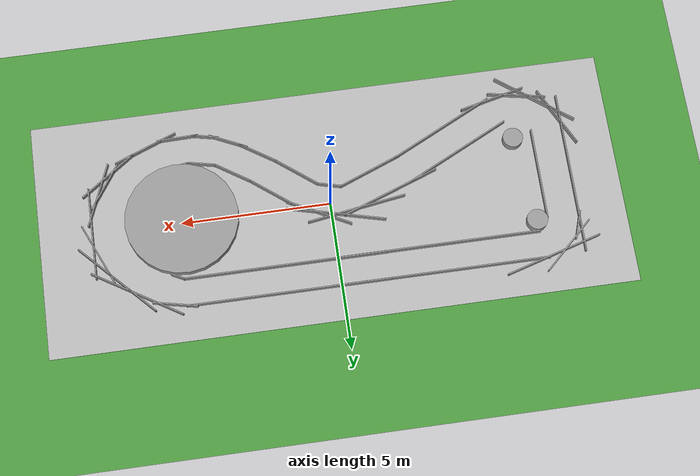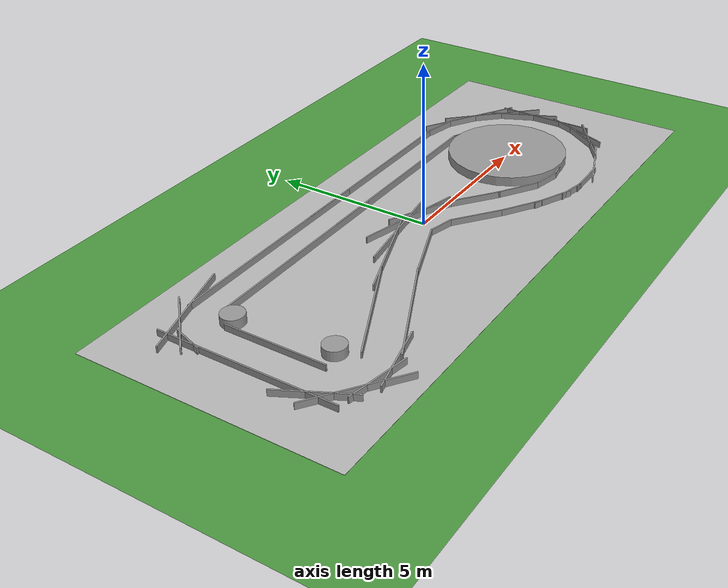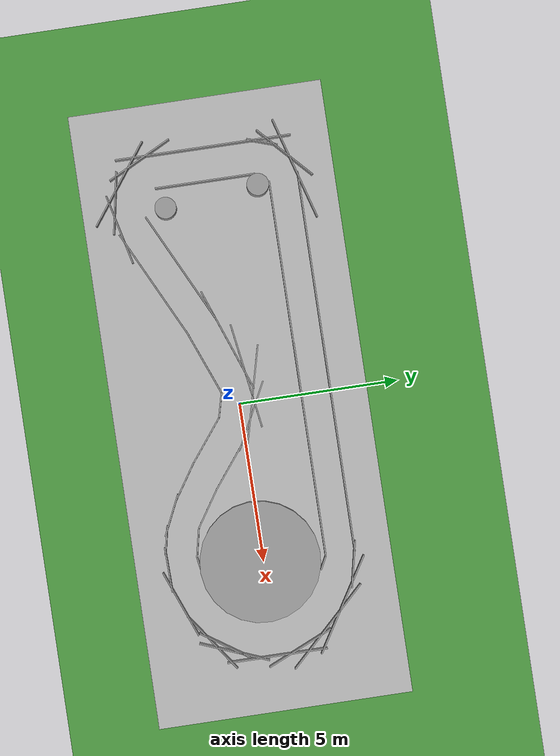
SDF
<sdf version="1.5">
 <world name="default">
  <light name="sun" type="directional">
   <cast_shadows>0</cast_shadows>
   <pose>0 0 10 0 -0 0</pose>
   <diffuse>0.8 0.8 0.8 1</diffuse>
   <specular>0.2 0.2 0.2 1</specular>
   <attenuation>
    <range>1000</range>
    <constant>0.9</constant>
    <linear>0.01</linear>
    <quadratic>0.001</quadratic>
   </attenuation>
   <direction>-0.5 0.1 -0.9</direction>
  </light>
  <scene>
   <sky><clouds><speed>1</speed></clouds></sky>
   <ambient>0.4 0.4 0.4 1</ambient>
   <background>0.7 0.7 0.7 1</background>
   <shadows>1</shadows>
  </scene>
  <physics name="default_physics" default="0" type="ode">
   <real_time_update_rate>1000</real_time_update_rate>
   <ode>
    <solver>
     <type>quick</type>
     <iters>70</iters>
     <sor>1.3</sor>
     <use_dynamic_moi_rescaling>0</use_dynamic_moi_rescaling>
    </solver>
    <constraints>
     <cfm>0</cfm>
     <erp>0.2</erp>
     <contact_max_correcting_vel>100</contact_max_correcting_vel>
     <contact_surface_layer>0.001</contact_surface_layer>
    </constraints>
   </ode>
   <max_step_size>0.001</max_step_size>
   <real_time_factor>1</real_time_factor>
  </physics>
  <scene><ambient>0.4 0.4 0.4 1</ambient><background>0.7 0.7 0.7 1</background><shadows>1</shadows></scene>
  <spherical_coordinates>
   <surface_model>EARTH_WGS84</surface_model>
   <latitude_deg>0</latitude_deg>
   <longitude_deg>0</longitude_deg>
   <elevation>0</elevation>
   <heading_deg>0</heading_deg>
  </spherical_coordinates>
  <model name="ground_grass">
   <static>1</static>
   <link name="ground_grass">
    <collision name="collision">
     <geometry><plane><normal>0 0 1</normal><size>50 50</size></plane></geometry>
     <surface><friction><ode><mu>100</mu><mu2>50</mu2></ode></friction></surface>
    </collision>
    <visual name="visual_ground">
     <cast_shadows>0</cast_shadows>
     <pose>0 0 0.005 0 -0 0</pose>
     <geometry><plane><normal>0 0 1</normal><size>50 50</size></plane></geometry>
     <material>
      <script>
       <uri>model://ground_grass/materials/scripts</uri>
       <uri>model://ground_grass/materials/textures</uri>
       <name>Floor/Grass</name>
      </script>
     </material>
    </visual>
    <velocity_decay><linear>0</linear><angular>0</angular></velocity_decay>
   </link>
  </model>
  <model name="ucsd_track_v1">
   <static>1</static>
   <link name="link_track">
    <collision name="collision">
     <geometry><plane><normal>0 0 1</normal><size>19.431 8.0264</size></plane></geometry>
     <surface><friction><ode><mu>100</mu><mu2>50</mu2></ode></friction></surface>
    </collision>
    <visual name="visual_ground">
     <cast_shadows>0</cast_shadows>
     <pose>0 0 0.005 0 -0 0</pose>
     <geometry><plane><normal>0 0 1</normal><size>19.431 8.0264</size></plane></geometry>
     <material>
      <script>
       <uri>model://ucsd_track_v1/materials/scripts</uri>
       <uri>model://ucsd_track_v1/materials/textures</uri>
       <name>Floor/Image</name>
      </script>
     </material>
    </visual>
    <velocity_decay><linear>0</linear><angular>0</angular></velocity_decay>
   </link>
   <pose>0 0 0.001 0 -0 0</pose>
  </model>
  <gravity>0 0 -9.8</gravity>
  <magnetic_field>6e-06 2.3e-05 -4.2e-05</magnetic_field>
  <atmosphere type="adiabatic"/>
  <model name="grey_wall_track">
   <link name="link">
    <pose>0 0 1.4 0 -0 0</pose>
    <inertial>
     <inertia><ixx>nan</ixx><ixy>0</ixy><ixz>0</ixz><iyy>nan</iyy><iyz>0</iyz><izz>nan</izz></inertia>
     <mass>0</mass>
    </inertial>
    <visual name="visual">
     <cast_shadows>0</cast_shadows>
     <geometry><box><size>6.7262 0.043266 0.226147</size></box></geometry>
     <material>
      <script>
       <uri>model://grey_wall/materials/scripts</uri>
       <uri>model://grey_wall/materials/textures</uri>
       <name>vrc/grey_wall</name>
      </script>
      <ambient>1 1 1 1</ambient>
      <diffuse>1 1 1 1</diffuse>
      <specular>0 0 0 1</specular>
      <emissive>0 0 0 1</emissive>
     </material>
    </visual>
    <collision name="collision">
     <geometry><box><size>6.7262 0.043266 0.226147</size></box></geometry>
     <surface>
      <friction>
       <ode><mu>1</mu><mu2>1</mu2><fdir1>0 0 0</fdir1><slip1>0</slip1><slip2>0</slip2></ode>
       <torsional>
        <coefficient>1</coefficient>
        <patch_radius>0</patch_radius>
        <surface_radius>0</surface_radius>
        <use_patch_radius>1</use_patch_radius>
        <ode><slip>0</slip></ode>
       </torsional>
      </friction>
      <bounce><restitution_coefficient>0</restitution_coefficient><threshold>1e+06</threshold></bounce>
      <contact>
       <collide_without_contact>0</collide_without_contact>
       <collide_without_contact_bitmask>1</collide_without_contact_bitmask>
       <collide_bitmask>1</collide_bitmask>
       <ode>
        <soft_cfm>0</soft_cfm>
        <soft_erp>0.2</soft_erp>
        <kp>1e+13</kp>
        <kd>1</kd>
        <max_vel>0.01</max_vel>
        <min_depth>0</min_depth>
       </ode>
       <bullet>
        <split_impulse>1</split_impulse>
        <split_impulse_penetration_threshold>-0.01</split_impulse_penetration_threshold>
        <soft_cfm>0</soft_cfm>
        <soft_erp>0.2</soft_erp>
        <kp>1e+13</kp>
        <kd>1</kd>
       </bullet>
      </contact>
     </surface>
    </collision>
   </link>
   <static>1</static>
   <pose>-3.38545 1.93605 -1.28591 0 -0 0</pose>
  </model>
  <model name="grey_wall_track_1">
   <link name="link">
    <pose>0 0 1.4 0 -0 0</pose>
    <inertial>
     <inertia><ixx>nan</ixx><ixy>0</ixy><ixz>0</ixz><iyy>nan</iyy><iyz>0</iyz><izz>nan</izz></inertia>
     <mass>0</mass>
    </inertial>
    <visual name="visual">
     <cast_shadows>0</cast_shadows>
     <geometry><box><size>6.7262 0.043266 0.226147</size></box></geometry>
     <material>
      <script>
       <uri>model://grey_wall/materials/scripts</uri>
       <uri>model://grey_wall/materials/textures</uri>
       <name>vrc/grey_wall</name>
      </script>
      <ambient>1 1 1 1</ambient>
      <diffuse>1 1 1 1</diffuse>
      <specular>0 0 0 1</specular>
      <emissive>0 0 0 1</emissive>
     </material>
    </visual>
    <collision name="collision">
     <geometry><box><size>6.7262 0.043266 0.226147</size></box></geometry>
     <surface>
      <friction>
       <ode><mu>1</mu><mu2>1</mu2><fdir1>0 0 0</fdir1><slip1>0</slip1><slip2>0</slip2></ode>
       <torsional>
        <coefficient>1</coefficient>
        <patch_radius>0</patch_radius>
        <surface_radius>0</surface_radius>
        <use_patch_radius>1</use_patch_radius>
        <ode><slip>0</slip></ode>
       </torsional>
      </friction>
      <bounce><restitution_coefficient>0</restitution_coefficient><threshold>1e+06</threshold></bounce>
      <contact>
       <collide_without_contact>0</collide_without_contact>
       <collide_without_contact_bitmask>1</collide_without_contact_bitmask>
       <collide_bitmask>1</collide_bitmask>
       <ode>
        <soft_cfm>0</soft_cfm>
        <soft_erp>0.2</soft_erp>
        <kp>1e+13</kp>
        <kd>1</kd>
        <max_vel>0.01</max_vel>
        <min_depth>0</min_depth>
       </ode>
       <bullet>
        <split_impulse>1</split_impulse>
        <split_impulse_penetration_threshold>-0.01</split_impulse_penetration_threshold>
        <soft_cfm>0</soft_cfm>
        <soft_erp>0.2</soft_erp>
        <kp>1e+13</kp>
        <kd>1</kd>
       </bullet>
      </contact>
     </surface>
    </collision>
   </link>
   <static>1</static>
   <pose>1.7337 1.94342 -1.28559 0 -0 0</pose>
  </model>
  <model name="grey_wall_track_2">
   <link name="link">
    <pose>0 0 1.4 0 -0 0</pose>
    <inertial>
     <inertia><ixx>nan</ixx><ixy>0</ixy><ixz>0</ixz><iyy>nan</iyy><iyz>0</iyz><izz>nan</izz></inertia>
     <mass>0</mass>
    </inertial>
    <visual name="visual">
     <cast_shadows>0</cast_shadows>
     <geometry><box><size>6.7262 0.043266 0.226147</size></box></geometry>
     <material>
      <script>
       <uri>model://grey_wall/materials/scripts</uri>
       <uri>model://grey_wall/materials/textures</uri>
       <name>vrc/grey_wall</name>
      </script>
      <ambient>1 1 1 1</ambient>
      <diffuse>1 1 1 1</diffuse>
      <specular>0 0 0 1</specular>
      <emissive>0 0 0 1</emissive>
     </material>
    </visual>
    <collision name="collision">
     <geometry><box><size>6.7262 0.043266 0.226147</size></box></geometry>
     <surface>
      <friction>
       <ode><mu>1</mu><mu2>1</mu2><fdir1>0 0 0</fdir1><slip1>0</slip1><slip2>0</slip2></ode>
       <torsional>
        <coefficient>1</coefficient>
        <patch_radius>0</patch_radius>
        <surface_radius>0</surface_radius>
        <use_patch_radius>1</use_patch_radius>
        <ode><slip>0</slip></ode>
       </torsional>
      </friction>
      <bounce><restitution_coefficient>0</restitution_coefficient><threshold>1e+06</threshold></bounce>
      <contact>
       <collide_without_contact>0</collide_without_contact>
       <collide_without_contact_bitmask>1</collide_without_contact_bitmask>
       <collide_bitmask>1</collide_bitmask>
       <ode>
        <soft_cfm>0</soft_cfm>
        <soft_erp>0.2</soft_erp>
        <kp>1e+13</kp>
        <kd>1</kd>
        <max_vel>0.01</max_vel>
        <min_depth>0</min_depth>
       </ode>
       <bullet>
        <split_impulse>1</split_impulse>
        <split_impulse_penetration_threshold>-0.01</split_impulse_penetration_threshold>
        <soft_cfm>0</soft_cfm>
        <soft_erp>0.2</soft_erp>
        <kp>1e+13</kp>
        <kd>1</kd>
       </bullet>
      </contact>
     </surface>
    </collision>
   </link>
   <static>1</static>
   <pose>1.73864 2.86141 -1.30508 0 -0 0</pose>
  </model>
  <model name="grey_wall_small_6">
   <link name="link">
    <pose>0 0 1.4 0 -0 0.009516</pose>
    <inertial>
     <inertia><ixx>nan</ixx><ixy>0</ixy><ixz>0</ixz><iyy>nan</iyy><iyz>0</iyz><izz>nan</izz></inertia>
     <mass>0</mass>
    </inertial>
    <visual name="visual">
     <cast_shadows>0</cast_shadows>
     <geometry><box><size>3.14897 0.043266 0.226147</size></box></geometry>
     <material>
      <script>
       <uri>model://grey_wall/materials/scripts</uri>
       <uri>model://grey_wall/materials/textures</uri>
       <name>vrc/grey_wall</name>
      </script>
      <ambient>1 1 1 1</ambient>
      <diffuse>1 1 1 1</diffuse>
      <specular>0 0 0 1</specular>
      <emissive>0 0 0 1</emissive>
     </material>
    </visual>
    <collision name="collision">
     <geometry><box><size>3.14897 0.043266 0.226147</size></box></geometry>
     <surface>
      <friction>
       <ode><mu>1</mu><mu2>1</mu2><fdir1>0 0 0</fdir1><slip1>0</slip1><slip2>0</slip2></ode>
       <torsional>
        <coefficient>1</coefficient>
        <patch_radius>0</patch_radius>
        <surface_radius>0</surface_radius>
        <use_patch_radius>1</use_patch_radius>
        <ode><slip>0</slip></ode>
       </torsional>
      </friction>
      <bounce><restitution_coefficient>0</restitution_coefficient><threshold>1e+06</threshold></bounce>
      <contact>
       <collide_without_contact>0</collide_without_contact>
       <collide_without_contact_bitmask>1</collide_without_contact_bitmask>
       <collide_bitmask>1</collide_bitmask>
       <ode>
        <soft_cfm>0</soft_cfm>
        <soft_erp>0.2</soft_erp>
        <kp>1e+13</kp>
        <kd>1</kd>
        <max_vel>0.01</max_vel>
        <min_depth>0</min_depth>
       </ode>
       <bullet>
        <split_impulse>1</split_impulse>
        <split_impulse_penetration_threshold>-0.01</split_impulse_penetration_threshold>
        <soft_cfm>0</soft_cfm>
        <soft_erp>0.2</soft_erp>
        <kp>1e+13</kp>
        <kd>1</kd>
       </bullet>
      </contact>
     </surface>
    </collision>
   </link>
   <static>1</static>
   <pose>-7.05702 -0.045658 -1.30963 0 -0 1.55954</pose>
  </model>
  <model name="grey_wall_twisted_s_2">
   <link name="link">
    <pose>0 0 1.4 0 0 -0.580025</pose>
    <inertial>
     <inertia><ixx>nan</ixx><ixy>0</ixy><ixz>0</ixz><iyy>nan</iyy><iyz>0</iyz><izz>nan</izz></inertia>
     <mass>0</mass>
    </inertial>
    <visual name="visual">
     <cast_shadows>0</cast_shadows>
     <geometry><box><size>1.36861 0.043266 0.226147</size></box></geometry>
     <material>
      <script>
       <uri>model://grey_wall/materials/scripts</uri>
       <uri>model://grey_wall/materials/textures</uri>
       <name>vrc/grey_wall</name>
      </script>
      <ambient>1 1 1 1</ambient>
      <diffuse>1 1 1 1</diffuse>
      <specular>0 0 0 1</specular>
      <emissive>0 0 0 1</emissive>
     </material>
    </visual>
    <collision name="collision">
     <geometry><box><size>1.36861 0.043266 0.226147</size></box></geometry>
     <surface>
      <friction>
       <ode><mu>1</mu><mu2>1</mu2><fdir1>0 0 0</fdir1><slip1>0</slip1><slip2>0</slip2></ode>
       <torsional>
        <coefficient>1</coefficient>
        <patch_radius>0</patch_radius>
        <surface_radius>0</surface_radius>
        <use_patch_radius>1</use_patch_radius>
        <ode><slip>0</slip></ode>
       </torsional>
      </friction>
      <bounce><restitution_coefficient>0</restitution_coefficient><threshold>1e+06</threshold></bounce>
      <contact>
       <collide_without_contact>0</collide_without_contact>
       <collide_without_contact_bitmask>1</collide_without_contact_bitmask>
       <collide_bitmask>1</collide_bitmask>
       <ode>
        <soft_cfm>0</soft_cfm>
        <soft_erp>0.2</soft_erp>
        <kp>1e+13</kp>
        <kd>1</kd>
        <max_vel>0.01</max_vel>
        <min_depth>0</min_depth>
       </ode>
       <bullet>
        <split_impulse>1</split_impulse>
        <split_impulse_penetration_threshold>-0.01</split_impulse_penetration_threshold>
        <soft_cfm>0</soft_cfm>
        <soft_erp>0.2</soft_erp>
        <kp>1e+13</kp>
        <kd>1</kd>
       </bullet>
      </contact>
     </surface>
    </collision>
   </link>
   <static>1</static>
   <pose>3.08955 -1.47755 -1.30469 0 -0 0</pose>
  </model>
  <model name="grey_wall_twisted_z_4">
   <link name="link">
    <pose>0 0 1.4 0 0 -0.211768</pose>
    <inertial>
     <inertia><ixx>nan</ixx><ixy>0</ixy><ixz>0</ixz><iyy>nan</iyy><iyz>0</iyz><izz>nan</izz></inertia>
     <mass>0</mass>
    </inertial>
    <visual name="visual">
     <cast_shadows>0</cast_shadows>
     <geometry><box><size>0.9086 0.043266 0.226147</size></box></geometry>
     <material>
      <script>
       <uri>model://grey_wall/materials/scripts</uri>
       <uri>model://grey_wall/materials/textures</uri>
       <name>vrc/grey_wall</name>
      </script>
      <ambient>1 1 1 1</ambient>
      <diffuse>1 1 1 1</diffuse>
      <specular>0 0 0 1</specular>
      <emissive>0 0 0 1</emissive>
     </material>
    </visual>
    <collision name="collision">
     <geometry><box><size>0.9086 0.043266 0.226147</size></box></geometry>
     <surface>
      <friction>
       <ode><mu>1</mu><mu2>1</mu2><fdir1>0 0 0</fdir1><slip1>0</slip1><slip2>0</slip2></ode>
       <torsional>
        <coefficient>1</coefficient>
        <patch_radius>0</patch_radius>
        <surface_radius>0</surface_radius>
        <use_patch_radius>1</use_patch_radius>
        <ode><slip>0</slip></ode>
       </torsional>
      </friction>
      <bounce><restitution_coefficient>0</restitution_coefficient><threshold>1e+06</threshold></bounce>
      <contact>
       <collide_without_contact>0</collide_without_contact>
       <collide_without_contact_bitmask>1</collide_without_contact_bitmask>
       <collide_bitmask>1</collide_bitmask>
       <ode>
        <soft_cfm>0</soft_cfm>
        <soft_erp>0.2</soft_erp>
        <kp>1e+13</kp>
        <kd>1</kd>
        <max_vel>0.01</max_vel>
        <min_depth>0</min_depth>
       </ode>
       <bullet>
        <split_impulse>1</split_impulse>
        <split_impulse_penetration_threshold>-0.01</split_impulse_penetration_threshold>
        <soft_cfm>0</soft_cfm>
        <soft_erp>0.2</soft_erp>
        <kp>1e+13</kp>
        <kd>1</kd>
       </bullet>
      </contact>
     </surface>
    </collision>
   </link>
   <static>1</static>
   <pose>4.09788 -1.94353 -1.30469 0 -0 0</pose>
  </model>
  <model name="unit_cylinder2_1">
   <link name="link">
    <inertial>
     <mass>0.30371</mass>
     <inertia>
      <ixx>0.0213162</ixx>
      <ixy>0</ixy>
      <ixz>0</ixz>
      <iyy>0.0213162</iyy>
      <iyz>0</iyz>
      <izz>0.0379638</izz>
     </inertia>
    </inertial>
    <visual name="visual">
     <geometry><cylinder><radius>0.348419</radius><length>0.303709</length></cylinder></geometry>
     <material>
      <script><name>Gazebo/Grey</name><uri>file://media/materials/scripts/gazebo.material</uri></script>
      <ambient>0.3 0.3 0.3 1</ambient>
      <diffuse>0.7 0.7 0.7 1</diffuse>
      <specular>0.01 0.01 0.01 1</specular>
      <emissive>0 0 0 1</emissive>
     </material>
    </visual>
    <collision name="collision">
     <geometry><cylinder><radius>0.348419</radius><length>0.303709</length></cylinder></geometry>
     <surface>
      <friction>
       <ode><mu>1</mu><mu2>1</mu2><fdir1>0 0 0</fdir1><slip1>0</slip1><slip2>0</slip2></ode>
       <torsional>
        <coefficient>1</coefficient>
        <patch_radius>0</patch_radius>
        <surface_radius>0</surface_radius>
        <use_patch_radius>1</use_patch_radius>
        <ode><slip>0</slip></ode>
       </torsional>
      </friction>
      <bounce><restitution_coefficient>0</restitution_coefficient><threshold>1e+06</threshold></bounce>
      <contact>
       <collide_without_contact>0</collide_without_contact>
       <collide_without_contact_bitmask>1</collide_without_contact_bitmask>
       <collide_bitmask>1</collide_bitmask>
       <ode>
        <soft_cfm>0</soft_cfm>
        <soft_erp>0.2</soft_erp>
        <kp>1e+13</kp>
        <kd>1</kd>
        <max_vel>0.01</max_vel>
        <min_depth>0</min_depth>
       </ode>
       <bullet>
        <split_impulse>1</split_impulse>
        <split_impulse_penetration_threshold>-0.01</split_impulse_penetration_threshold>
        <soft_cfm>0</soft_cfm>
        <soft_erp>0.2</soft_erp>
        <kp>1e+13</kp>
        <kd>1</kd>
       </bullet>
      </contact>
     </surface>
    </collision>
   </link>
   <static>0</static>
   <pose>-6.68593 1.56597 0.152854 0 -0 0.015083</pose>
  </model>
  <model name="unit_cylinder1">
   <link name="link">
    <inertial>
     <mass>0.30371</mass>
     <inertia>
      <ixx>0.0213162</ixx>
      <ixy>0</ixy>
      <ixz>0</ixz>
      <iyy>0.0213162</iyy>
      <iyz>0</iyz>
      <izz>0.0379638</izz>
     </inertia>
    </inertial>
    <visual name="visual">
     <geometry><cylinder><radius>0.339812</radius><length>0.303709</length></cylinder></geometry>
     <material>
      <script><name>Gazebo/Grey</name><uri>file://media/materials/scripts/gazebo.material</uri></script>
      <ambient>0.3 0.3 0.3 1</ambient>
      <diffuse>0.7 0.7 0.7 1</diffuse>
      <specular>0.01 0.01 0.01 1</specular>
      <emissive>0 0 0 1</emissive>
     </material>
    </visual>
    <collision name="collision">
     <geometry><cylinder><radius>0.339812</radius><length>0.303709</length></cylinder></geometry>
     <surface>
      <friction>
       <ode><mu>1</mu><mu2>1</mu2><fdir1>0 0 0</fdir1><slip1>0</slip1><slip2>0</slip2></ode>
       <torsional>
        <coefficient>1</coefficient>
        <patch_radius>0</patch_radius>
        <surface_radius>0</surface_radius>
        <use_patch_radius>1</use_patch_radius>
        <ode><slip>0</slip></ode>
       </torsional>
      </friction>
      <bounce><restitution_coefficient>0</restitution_coefficient><threshold>1e+06</threshold></bounce>
      <contact>
       <collide_without_contact>0</collide_without_contact>
       <collide_without_contact_bitmask>1</collide_without_contact_bitmask>
       <collide_bitmask>1</collide_bitmask>
       <ode>
        <soft_cfm>0</soft_cfm>
        <soft_erp>0.2</soft_erp>
        <kp>1e+13</kp>
        <kd>1</kd>
        <max_vel>0.01</max_vel>
        <min_depth>0</min_depth>
       </ode>
       <bullet>
        <split_impulse>1</split_impulse>
        <split_impulse_penetration_threshold>-0.01</split_impulse_penetration_threshold>
        <soft_cfm>0</soft_cfm>
        <soft_erp>0.2</soft_erp>
        <kp>1e+13</kp>
        <kd>1</kd>
       </bullet>
      </contact>
     </surface>
    </collision>
   </link>
   <static>0</static>
   <pose>-6.38487 -1.38439 0.152854 0 -0 0.049949</pose>
  </model>
  <model name="unit_cylinder3">
   <link name="link">
    <inertial>
     <mass>0.30371</mass>
     <inertia>
      <ixx>0.0213162</ixx>
      <ixy>0</ixy>
      <ixz>0</ixz>
      <iyy>0.0213162</iyy>
      <iyz>0</iyz>
      <izz>0.0379638</izz>
     </inertia>
    </inertial>
    <visual name="visual">
     <geometry><cylinder><radius>1.89087</radius><length>0.303709</length></cylinder></geometry>
     <material>
      <script><name>Gazebo/Grey</name><uri>file://media/materials/scripts/gazebo.material</uri></script>
      <ambient>0.3 0.3 0.3 1</ambient>
      <diffuse>0.7 0.7 0.7 1</diffuse>
      <specular>0.01 0.01 0.01 1</specular>
      <emissive>0 0 0 1</emissive>
     </material>
    </visual>
    <collision name="collision">
     <geometry><cylinder><radius>1.89087</radius><length>0.303709</length></cylinder></geometry>
     <surface>
      <friction>
       <ode><mu>1</mu><mu2>1</mu2><fdir1>0 0 0</fdir1><slip1>0</slip1><slip2>0</slip2></ode>
       <torsional>
        <coefficient>1</coefficient>
        <patch_radius>0</patch_radius>
        <surface_radius>0</surface_radius>
        <use_patch_radius>1</use_patch_radius>
        <ode><slip>0</slip></ode>
       </torsional>
      </friction>
      <bounce><restitution_coefficient>0</restitution_coefficient><threshold>1e+06</threshold></bounce>
      <contact>
       <collide_without_contact>0</collide_without_contact>
       <collide_without_contact_bitmask>1</collide_without_contact_bitmask>
       <collide_bitmask>1</collide_bitmask>
       <ode>
        <soft_cfm>0</soft_cfm>
        <soft_erp>0.2</soft_erp>
        <kp>1e+13</kp>
        <kd>1</kd>
        <max_vel>0.01</max_vel>
        <min_depth>0</min_depth>
       </ode>
       <bullet>
        <split_impulse>1</split_impulse>
        <split_impulse_penetration_threshold>-0.01</split_impulse_penetration_threshold>
        <soft_cfm>0</soft_cfm>
        <soft_erp>0.2</soft_erp>
        <kp>1e+13</kp>
        <kd>1</kd>
       </bullet>
      </contact>
     </surface>
    </collision>
   </link>
   <static>0</static>
   <pose>4.95647 -0.103734 0.152854 0 -0 0.04995</pose>
  </model>
  <model name="grey_wall_twisted_b_3">
   <link name="link">
    <pose>0 0 1.4 0 -0 0.168525</pose>
    <inertial>
     <inertia><ixx>nan</ixx><ixy>0</ixy><ixz>0</ixz><iyy>nan</iyy><iyz>0</iyz><izz>nan</izz></inertia>
     <mass>0</mass>
    </inertial>
    <visual name="visual">
     <cast_shadows>0</cast_shadows>
     <geometry><box><size>0.67315 0.043266 0.226147</size></box></geometry>
     <material>
      <script>
       <uri>model://grey_wall/materials/scripts</uri>
       <uri>model://grey_wall/materials/textures</uri>
       <name>vrc/grey_wall</name>
      </script>
      <ambient>1 1 1 1</ambient>
      <diffuse>1 1 1 1</diffuse>
      <specular>0 0 0 1</specular>
      <emissive>0 0 0 1</emissive>
     </material>
    </visual>
    <collision name="collision">
     <geometry><box><size>0.67315 0.043266 0.226147</size></box></geometry>
     <surface>
      <friction>
       <ode><mu>1</mu><mu2>1</mu2><fdir1>0 0 0</fdir1><slip1>0</slip1><slip2>0</slip2></ode>
       <torsional>
        <coefficient>1</coefficient>
        <patch_radius>0</patch_radius>
        <surface_radius>0</surface_radius>
        <use_patch_radius>1</use_patch_radius>
        <ode><slip>0</slip></ode>
       </torsional>
      </friction>
      <bounce><restitution_coefficient>0</restitution_coefficient><threshold>1e+06</threshold></bounce>
      <contact>
       <collide_without_contact>0</collide_without_contact>
       <collide_without_contact_bitmask>1</collide_without_contact_bitmask>
       <collide_bitmask>1</collide_bitmask>
       <ode>
        <soft_cfm>0</soft_cfm>
        <soft_erp>0.2</soft_erp>
        <kp>1e+13</kp>
        <kd>1</kd>
        <max_vel>0.01</max_vel>
        <min_depth>0</min_depth>
       </ode>
       <bullet>
        <split_impulse>1</split_impulse>
        <split_impulse_penetration_threshold>-0.01</split_impulse_penetration_threshold>
        <soft_cfm>0</soft_cfm>
        <soft_erp>0.2</soft_erp>
        <kp>1e+13</kp>
        <kd>1</kd>
       </bullet>
      </contact>
     </surface>
    </collision>
   </link>
   <static>1</static>
   <pose>4.8563 -1.98315 -1.30532 0 -0 0</pose>
  </model>
  <model name="grey_wall_twisted_c_0">
   <link name="link">
    <pose>0 0 1.4 0 0 -0.480065</pose>
    <inertial>
     <inertia><ixx>nan</ixx><ixy>0</ixy><ixz>0</ixz><iyy>nan</iyy><iyz>0</iyz><izz>nan</izz></inertia>
     <mass>0</mass>
    </inertial>
    <visual name="visual">
     <cast_shadows>0</cast_shadows>
     <geometry><box><size>0.469435 0.043266 0.261158</size></box></geometry>
     <material>
      <script>
       <uri>model://grey_wall/materials/scripts</uri>
       <uri>model://grey_wall/materials/textures</uri>
       <name>vrc/grey_wall</name>
      </script>
      <ambient>1 1 1 1</ambient>
      <diffuse>1 1 1 1</diffuse>
      <specular>0 0 0 1</specular>
      <emissive>0 0 0 1</emissive>
     </material>
    </visual>
    <collision name="collision">
     <geometry><box><size>0.469435 0.043266 0.261158</size></box></geometry>
     <surface>
      <friction>
       <ode><mu>1</mu><mu2>1</mu2><fdir1>0 0 0</fdir1><slip1>0</slip1><slip2>0</slip2></ode>
       <torsional>
        <coefficient>1</coefficient>
        <patch_radius>0</patch_radius>
        <surface_radius>0</surface_radius>
        <use_patch_radius>1</use_patch_radius>
        <ode><slip>0</slip></ode>
       </torsional>
      </friction>
      <bounce><restitution_coefficient>0</restitution_coefficient><threshold>1e+06</threshold></bounce>
      <contact>
       <collide_without_contact>0</collide_without_contact>
       <collide_without_contact_bitmask>1</collide_without_contact_bitmask>
       <collide_bitmask>1</collide_bitmask>
       <ode>
        <soft_cfm>0</soft_cfm>
        <soft_erp>0.2</soft_erp>
        <kp>1e+13</kp>
        <kd>1</kd>
        <max_vel>0.01</max_vel>
        <min_depth>0</min_depth>
       </ode>
       <bullet>
        <split_impulse>1</split_impulse>
        <split_impulse_penetration_threshold>-0.01</split_impulse_penetration_threshold>
        <soft_cfm>0</soft_cfm>
        <soft_erp>0.2</soft_erp>
        <kp>1e+13</kp>
        <kd>1</kd>
       </bullet>
      </contact>
     </surface>
    </collision>
   </link>
   <static>1</static>
   <pose>5.2931 1.83753 -1.30532 0 -0 0</pose>
  </model>
  <model name="grey_wall_twisted_s_1_0">
   <link name="link">
    <pose>0 0 1.4 0 0 -0.660395</pose>
    <inertial>
     <inertia><ixx>nan</ixx><ixy>0</ixy><ixz>0</ixz><iyy>nan</iyy><iyz>0</iyz><izz>nan</izz></inertia>
     <mass>0</mass>
    </inertial>
    <visual name="visual">
     <cast_shadows>0</cast_shadows>
     <geometry><box><size>1.62445 0.043266 0.226147</size></box></geometry>
     <material>
      <script>
       <uri>model://grey_wall/materials/scripts</uri>
       <uri>model://grey_wall/materials/textures</uri>
       <name>vrc/grey_wall</name>
      </script>
      <ambient>1 1 1 1</ambient>
      <diffuse>1 1 1 1</diffuse>
      <specular>0 0 0 1</specular>
      <emissive>0 0 0 1</emissive>
     </material>
    </visual>
    <collision name="collision">
     <geometry><box><size>1.62445 0.043266 0.226147</size></box></geometry>
     <surface>
      <friction>
       <ode><mu>1</mu><mu2>1</mu2><fdir1>0 0 0</fdir1><slip1>0</slip1><slip2>0</slip2></ode>
       <torsional>
        <coefficient>1</coefficient>
        <patch_radius>0</patch_radius>
        <surface_radius>0</surface_radius>
        <use_patch_radius>1</use_patch_radius>
        <ode><slip>0</slip></ode>
       </torsional>
      </friction>
      <bounce><restitution_coefficient>0</restitution_coefficient><threshold>1e+06</threshold></bounce>
      <contact>
       <collide_without_contact>0</collide_without_contact>
       <collide_without_contact_bitmask>1</collide_without_contact_bitmask>
       <collide_bitmask>1</collide_bitmask>
       <ode>
        <soft_cfm>0</soft_cfm>
        <soft_erp>0.2</soft_erp>
        <kp>1e+13</kp>
        <kd>1</kd>
        <max_vel>0.01</max_vel>
        <min_depth>0</min_depth>
       </ode>
       <bullet>
        <split_impulse>1</split_impulse>
        <split_impulse_penetration_threshold>-0.01</split_impulse_penetration_threshold>
        <soft_cfm>0</soft_cfm>
        <soft_erp>0.2</soft_erp>
        <kp>1e+13</kp>
        <kd>1</kd>
       </bullet>
      </contact>
     </surface>
    </collision>
   </link>
   <static>1</static>
   <pose>1.91984 -0.636241 -1.30469 0 -0 0</pose>
  </model>
  <model name="grey_wall_twisted_r_1_2">
   <link name="link">
    <pose>0 0 1.4 0 0 -0.470145</pose>
    <inertial>
     <inertia><ixx>nan</ixx><ixy>0</ixy><ixz>0</ixz><iyy>nan</iyy><iyz>0</iyz><izz>nan</izz></inertia>
     <mass>0</mass>
    </inertial>
    <visual name="visual">
     <cast_shadows>0</cast_shadows>
     <geometry><box><size>2.31434 0.043266 0.226147</size></box></geometry>
     <material>
      <script>
       <uri>model://grey_wall/materials/scripts</uri>
       <uri>model://grey_wall/materials/textures</uri>
       <name>vrc/grey_wall</name>
      </script>
      <ambient>1 1 1 1</ambient>
      <diffuse>1 1 1 1</diffuse>
      <specular>0 0 0 1</specular>
      <emissive>0 0 0 1</emissive>
     </material>
    </visual>
    <collision name="collision">
     <geometry><box><size>2.31434 0.043266 0.226147</size></box></geometry>
     <surface>
      <friction>
       <ode><mu>1</mu><mu2>1</mu2><fdir1>0 0 0</fdir1><slip1>0</slip1><slip2>0</slip2></ode>
       <torsional>
        <coefficient>1</coefficient>
        <patch_radius>0</patch_radius>
        <surface_radius>0</surface_radius>
        <use_patch_radius>1</use_patch_radius>
        <ode><slip>0</slip></ode>
       </torsional>
      </friction>
      <bounce><restitution_coefficient>0</restitution_coefficient><threshold>1e+06</threshold></bounce>
      <contact>
       <collide_without_contact>0</collide_without_contact>
       <collide_without_contact_bitmask>1</collide_without_contact_bitmask>
       <collide_bitmask>1</collide_bitmask>
       <ode>
        <soft_cfm>0</soft_cfm>
        <soft_erp>0.2</soft_erp>
        <kp>1e+13</kp>
        <kd>1</kd>
        <max_vel>0.01</max_vel>
        <min_depth>0</min_depth>
       </ode>
       <bullet>
        <split_impulse>1</split_impulse>
        <split_impulse_penetration_threshold>-0.01</split_impulse_penetration_threshold>
        <soft_cfm>0</soft_cfm>
        <soft_erp>0.2</soft_erp>
        <kp>1e+13</kp>
        <kd>1</kd>
       </bullet>
      </contact>
     </surface>
    </collision>
   </link>
   <static>1</static>
   <pose>0.423351 0.292484 -1.30552 0 -0 0</pose>
  </model>
  <model name="grey_wall_twisted_as">
   <link name="link">
    <pose>0 0 1.4 0 -0 0.150162</pose>
    <inertial>
     <inertia><ixx>nan</ixx><ixy>0</ixy><ixz>0</ixz><iyy>nan</iyy><iyz>0</iyz><izz>nan</izz></inertia>
     <mass>0</mass>
    </inertial>
    <visual name="visual">
     <cast_shadows>0</cast_shadows>
     <geometry><box><size>3.35542 0.043266 0.226147</size></box></geometry>
     <material>
      <script>
       <uri>model://grey_wall/materials/scripts</uri>
       <uri>model://grey_wall/materials/textures</uri>
       <name>vrc/grey_wall</name>
      </script>
      <ambient>1 1 1 1</ambient>
      <diffuse>1 1 1 1</diffuse>
      <specular>0 0 0 1</specular>
      <emissive>0 0 0 1</emissive>
     </material>
    </visual>
    <collision name="collision">
     <geometry><box><size>3.35542 0.043266 0.226147</size></box></geometry>
     <surface>
      <friction>
       <ode><mu>1</mu><mu2>1</mu2><fdir1>0 0 0</fdir1><slip1>0</slip1><slip2>0</slip2></ode>
       <torsional>
        <coefficient>1</coefficient>
        <patch_radius>0</patch_radius>
        <surface_radius>0</surface_radius>
        <use_patch_radius>1</use_patch_radius>
        <ode><slip>0</slip></ode>
       </torsional>
      </friction>
      <bounce><restitution_coefficient>0</restitution_coefficient><threshold>1e+06</threshold></bounce>
      <contact>
       <collide_without_contact>0</collide_without_contact>
       <collide_without_contact_bitmask>1</collide_without_contact_bitmask>
       <collide_bitmask>1</collide_bitmask>
       <ode>
        <soft_cfm>0</soft_cfm>
        <soft_erp>0.2</soft_erp>
        <kp>1e+13</kp>
        <kd>1</kd>
        <max_vel>0.01</max_vel>
        <min_depth>0</min_depth>
       </ode>
       <bullet>
        <split_impulse>1</split_impulse>
        <split_impulse_penetration_threshold>-0.01</split_impulse_penetration_threshold>
        <soft_cfm>0</soft_cfm>
        <soft_erp>0.2</soft_erp>
        <kp>1e+13</kp>
        <kd>1</kd>
       </bullet>
      </contact>
     </surface>
    </collision>
   </link>
   <static>1</static>
   <pose>-0.840468 0.32663 -1.30539 0 -0 0</pose>
  </model>
  <model name="grey_wall_twisted_3_cc">
   <link name="link">
    <pose>0 0 1.4 0 -0 0.351301</pose>
    <inertial>
     <inertia><ixx>nan</ixx><ixy>0</ixy><ixz>0</ixz><iyy>nan</iyy><iyz>0</iyz><izz>nan</izz></inertia>
     <mass>0</mass>
    </inertial>
    <visual name="visual">
     <cast_shadows>0</cast_shadows>
     <geometry><box><size>3.45281 0.043266 0.226147</size></box></geometry>
     <material>
      <script>
       <uri>model://grey_wall/materials/scripts</uri>
       <uri>model://grey_wall/materials/textures</uri>
       <name>vrc/grey_wall</name>
      </script>
      <ambient>1 1 1 1</ambient>
      <diffuse>1 1 1 1</diffuse>
      <specular>0 0 0 1</specular>
      <emissive>0 0 0 1</emissive>
     </material>
    </visual>
    <collision name="collision">
     <geometry><box><size>3.45281 0.043266 0.226147</size></box></geometry>
     <surface>
      <friction>
       <ode><mu>1</mu><mu2>1</mu2><fdir1>0 0 0</fdir1><slip1>0</slip1><slip2>0</slip2></ode>
       <torsional>
        <coefficient>1</coefficient>
        <patch_radius>0</patch_radius>
        <surface_radius>0</surface_radius>
        <use_patch_radius>1</use_patch_radius>
        <ode><slip>0</slip></ode>
       </torsional>
      </friction>
      <bounce><restitution_coefficient>0</restitution_coefficient><threshold>1e+06</threshold></bounce>
      <contact>
       <collide_without_contact>0</collide_without_contact>
       <collide_without_contact_bitmask>1</collide_without_contact_bitmask>
       <collide_bitmask>1</collide_bitmask>
       <ode>
        <soft_cfm>0</soft_cfm>
        <soft_erp>0.2</soft_erp>
        <kp>1e+13</kp>
        <kd>1</kd>
        <max_vel>0.01</max_vel>
        <min_depth>0</min_depth>
       </ode>
       <bullet>
        <split_impulse>1</split_impulse>
        <split_impulse_penetration_threshold>-0.01</split_impulse_penetration_threshold>
        <soft_cfm>0</soft_cfm>
        <soft_erp>0.2</soft_erp>
        <kp>1e+13</kp>
        <kd>1</kd>
       </bullet>
      </contact>
     </surface>
    </collision>
   </link>
   <static>1</static>
   <pose>-2.03101 -0.087839 -1.30331 0 -0 0</pose>
  </model>
  <model name="grey_wall_twisted_tf">
   <link name="link">
    <pose>0 0 1.4 0 -0 0.455224</pose>
    <inertial>
     <inertia><ixx>nan</ixx><ixy>0</ixy><ixz>0</ixz><iyy>nan</iyy><iyz>0</iyz><izz>nan</izz></inertia>
     <mass>0</mass>
    </inertial>
    <visual name="visual">
     <cast_shadows>0</cast_shadows>
     <geometry><box><size>3.81606 0.043266 0.226147</size></box></geometry>
     <material>
      <script>
       <uri>model://grey_wall/materials/scripts</uri>
       <uri>model://grey_wall/materials/textures</uri>
       <name>vrc/grey_wall</name>
      </script>
      <ambient>1 1 1 1</ambient>
      <diffuse>1 1 1 1</diffuse>
      <specular>0 0 0 1</specular>
      <emissive>0 0 0 1</emissive>
     </material>
    </visual>
    <collision name="collision">
     <geometry><box><size>3.81606 0.043266 0.226147</size></box></geometry>
     <surface>
      <friction>
       <ode><mu>1</mu><mu2>1</mu2><fdir1>0 0 0</fdir1><slip1>0</slip1><slip2>0</slip2></ode>
       <torsional>
        <coefficient>1</coefficient>
        <patch_radius>0</patch_radius>
        <surface_radius>0</surface_radius>
        <use_patch_radius>1</use_patch_radius>
        <ode><slip>0</slip></ode>
       </torsional>
      </friction>
      <bounce><restitution_coefficient>0</restitution_coefficient><threshold>1e+06</threshold></bounce>
      <contact>
       <collide_without_contact>0</collide_without_contact>
       <collide_without_contact_bitmask>1</collide_without_contact_bitmask>
       <collide_bitmask>1</collide_bitmask>
       <ode>
        <soft_cfm>0</soft_cfm>
        <soft_erp>0.2</soft_erp>
        <kp>1e+13</kp>
        <kd>1</kd>
        <max_vel>0.01</max_vel>
        <min_depth>0</min_depth>
       </ode>
       <bullet>
        <split_impulse>1</split_impulse>
        <split_impulse_penetration_threshold>-0.01</split_impulse_penetration_threshold>
        <soft_cfm>0</soft_cfm>
        <soft_erp>0.2</soft_erp>
        <kp>1e+13</kp>
        <kd>1</kd>
       </bullet>
      </contact>
     </surface>
    </collision>
   </link>
   <static>1</static>
   <pose>-4.49945 -1.20909 -1.30331 0 -0 0</pose>
  </model>
  <model name="grey_wall_twisted_as_fillin">
   <link name="link">
    <pose>0 0 1.4 0 0 -0.249614</pose>
    <inertial>
     <inertia><ixx>nan</ixx><ixy>0</ixy><ixz>0</ixz><iyy>nan</iyy><iyz>0</iyz><izz>nan</izz></inertia>
     <mass>0</mass>
    </inertial>
    <visual name="visual">
     <cast_shadows>0</cast_shadows>
     <geometry><box><size>3.35542 0.043266 0.226147</size></box></geometry>
     <material>
      <script>
       <uri>model://grey_wall/materials/scripts</uri>
       <uri>model://grey_wall/materials/textures</uri>
       <name>vrc/grey_wall</name>
      </script>
      <ambient>1 1 1 1</ambient>
      <diffuse>1 1 1 1</diffuse>
      <specular>0 0 0 1</specular>
      <emissive>0 0 0 1</emissive>
     </material>
    </visual>
    <collision name="collision">
     <geometry><box><size>3.35542 0.043266 0.226147</size></box></geometry>
     <surface>
      <friction>
       <ode><mu>1</mu><mu2>1</mu2><fdir1>0 0 0</fdir1><slip1>0</slip1><slip2>0</slip2></ode>
       <torsional>
        <coefficient>1</coefficient>
        <patch_radius>0</patch_radius>
        <surface_radius>0</surface_radius>
        <use_patch_radius>1</use_patch_radius>
        <ode><slip>0</slip></ode>
       </torsional>
      </friction>
      <bounce><restitution_coefficient>0</restitution_coefficient><threshold>1e+06</threshold></bounce>
      <contact>
       <collide_without_contact>0</collide_without_contact>
       <collide_without_contact_bitmask>1</collide_without_contact_bitmask>
       <collide_bitmask>1</collide_bitmask>
       <ode>
        <soft_cfm>0</soft_cfm>
        <soft_erp>0.2</soft_erp>
        <kp>1e+13</kp>
        <kd>1</kd>
        <max_vel>0.01</max_vel>
        <min_depth>0</min_depth>
       </ode>
       <bullet>
        <split_impulse>1</split_impulse>
        <split_impulse_penetration_threshold>-0.01</split_impulse_penetration_threshold>
        <soft_cfm>0</soft_cfm>
        <soft_erp>0.2</soft_erp>
        <kp>1e+13</kp>
        <kd>1</kd>
       </bullet>
      </contact>
     </surface>
    </collision>
   </link>
   <static>1</static>
   <pose>-0.129806 0.410559 -1.30539 0 -0 0</pose>
  </model>
  <model name="grey_wall_twisted_tf_clone">
   <link name="link">
    <pose>0 0 1.4 0 -0 0.455224</pose>
    <inertial>
     <inertia><ixx>nan</ixx><ixy>0</ixy><ixz>0</ixz><iyy>nan</iyy><iyz>0</iyz><izz>nan</izz></inertia>
     <mass>0</mass>
    </inertial>
    <visual name="visual">
     <cast_shadows>0</cast_shadows>
     <geometry><box><size>3.81606 0.043266 0.226147</size></box></geometry>
     <material>
      <script>
       <uri>model://grey_wall/materials/scripts</uri>
       <uri>model://grey_wall/materials/textures</uri>
       <name>vrc/grey_wall</name>
      </script>
      <ambient>1 1 1 1</ambient>
      <diffuse>1 1 1 1</diffuse>
      <specular>0 0 0 1</specular>
      <emissive>0 0 0 1</emissive>
     </material>
    </visual>
    <collision name="collision">
     <geometry><box><size>3.81606 0.043266 0.226147</size></box></geometry>
     <surface>
      <friction>
       <ode><mu>1</mu><mu2>1</mu2><fdir1>0 0 0</fdir1><slip1>0</slip1><slip2>0</slip2></ode>
       <torsional>
        <coefficient>1</coefficient>
        <patch_radius>0</patch_radius>
        <surface_radius>0</surface_radius>
        <use_patch_radius>1</use_patch_radius>
        <ode><slip>0</slip></ode>
       </torsional>
      </friction>
      <bounce><restitution_coefficient>0</restitution_coefficient><threshold>1e+06</threshold></bounce>
      <contact>
       <collide_without_contact>0</collide_without_contact>
       <collide_without_contact_bitmask>1</collide_without_contact_bitmask>
       <collide_bitmask>1</collide_bitmask>
       <ode>
        <soft_cfm>0</soft_cfm>
        <soft_erp>0.2</soft_erp>
        <kp>1e+13</kp>
        <kd>1</kd>
        <max_vel>0.01</max_vel>
        <min_depth>0</min_depth>
       </ode>
       <bullet>
        <split_impulse>1</split_impulse>
        <split_impulse_penetration_threshold>-0.01</split_impulse_penetration_threshold>
        <soft_cfm>0</soft_cfm>
        <soft_erp>0.2</soft_erp>
        <kp>1e+13</kp>
        <kd>1</kd>
       </bullet>
      </contact>
     </surface>
    </collision>
   </link>
   <static>1</static>
   <pose>-4.07016 -2.10177 -1.30331 0 -0 0</pose>
  </model>
  <model name="grey_wall_twisted_s_1_0_clone">
   <link name="link">
    <pose>0 0 1.4 0 0 -0.660395</pose>
    <inertial>
     <inertia><ixx>nan</ixx><ixy>0</ixy><ixz>0</ixz><iyy>nan</iyy><iyz>0</iyz><izz>nan</izz></inertia>
     <mass>0</mass>
    </inertial>
    <visual name="visual">
     <cast_shadows>0</cast_shadows>
     <geometry><box><size>1.62445 0.043266 0.226147</size></box></geometry>
     <material>
      <script>
       <uri>model://grey_wall/materials/scripts</uri>
       <uri>model://grey_wall/materials/textures</uri>
       <name>vrc/grey_wall</name>
      </script>
      <ambient>1 1 1 1</ambient>
      <diffuse>1 1 1 1</diffuse>
      <specular>0 0 0 1</specular>
      <emissive>0 0 0 1</emissive>
     </material>
    </visual>
    <collision name="collision">
     <geometry><box><size>1.62445 0.043266 0.226147</size></box></geometry>
     <surface>
      <friction>
       <ode><mu>1</mu><mu2>1</mu2><fdir1>0 0 0</fdir1><slip1>0</slip1><slip2>0</slip2></ode>
       <torsional>
        <coefficient>1</coefficient>
        <patch_radius>0</patch_radius>
        <surface_radius>0</surface_radius>
        <use_patch_radius>1</use_patch_radius>
        <ode><slip>0</slip></ode>
       </torsional>
      </friction>
      <bounce><restitution_coefficient>0</restitution_coefficient><threshold>1e+06</threshold></bounce>
      <contact>
       <collide_without_contact>0</collide_without_contact>
       <collide_without_contact_bitmask>1</collide_without_contact_bitmask>
       <collide_bitmask>1</collide_bitmask>
       <ode>
        <soft_cfm>0</soft_cfm>
        <soft_erp>0.2</soft_erp>
        <kp>1e+13</kp>
        <kd>1</kd>
        <max_vel>0.01</max_vel>
        <min_depth>0</min_depth>
       </ode>
       <bullet>
        <split_impulse>1</split_impulse>
        <split_impulse_penetration_threshold>-0.01</split_impulse_penetration_threshold>
        <soft_cfm>0</soft_cfm>
        <soft_erp>0.2</soft_erp>
        <kp>1e+13</kp>
        <kd>1</kd>
       </bullet>
      </contact>
     </surface>
    </collision>
   </link>
   <static>1</static>
   <pose>0.973487 -1.21034 -1.30469 0 -0 0</pose>
  </model>
  <model name="grey_wall_twisted_sm">
   <link name="link">
    <pose>0 0 1.4 0 0 -0.249614</pose>
    <inertial>
     <inertia><ixx>nan</ixx><ixy>0</ixy><ixz>0</ixz><iyy>nan</iyy><iyz>0</iyz><izz>nan</izz></inertia>
     <mass>0</mass>
    </inertial>
    <visual name="visual">
     <cast_shadows>0</cast_shadows>
     <geometry><box><size>0.794827 0.043266 0.226147</size></box></geometry>
     <material>
      <script>
       <uri>model://grey_wall/materials/scripts</uri>
       <uri>model://grey_wall/materials/textures</uri>
       <name>vrc/grey_wall</name>
      </script>
      <ambient>1 1 1 1</ambient>
      <diffuse>1 1 1 1</diffuse>
      <specular>0 0 0 1</specular>
      <emissive>0 0 0 1</emissive>
     </material>
    </visual>
    <collision name="collision">
     <geometry><box><size>0.794827 0.043266 0.226147</size></box></geometry>
     <surface>
      <friction>
       <ode><mu>1</mu><mu2>1</mu2><fdir1>0 0 0</fdir1><slip1>0</slip1><slip2>0</slip2></ode>
       <torsional>
        <coefficient>1</coefficient>
        <patch_radius>0</patch_radius>
        <surface_radius>0</surface_radius>
        <use_patch_radius>1</use_patch_radius>
        <ode><slip>0</slip></ode>
       </torsional>
      </friction>
      <bounce><restitution_coefficient>0</restitution_coefficient><threshold>1e+06</threshold></bounce>
      <contact>
       <collide_without_contact>0</collide_without_contact>
       <collide_without_contact_bitmask>1</collide_without_contact_bitmask>
       <collide_bitmask>1</collide_bitmask>
       <ode>
        <soft_cfm>0</soft_cfm>
        <soft_erp>0.2</soft_erp>
        <kp>1e+13</kp>
        <kd>1</kd>
        <max_vel>0.01</max_vel>
        <min_depth>0</min_depth>
       </ode>
       <bullet>
        <split_impulse>1</split_impulse>
        <split_impulse_penetration_threshold>-0.01</split_impulse_penetration_threshold>
        <soft_cfm>0</soft_cfm>
        <soft_erp>0.2</soft_erp>
        <kp>1e+13</kp>
        <kd>1</kd>
       </bullet>
      </contact>
     </surface>
    </collision>
   </link>
   <static>1</static>
   <pose>-0.042418 -0.617739 -1.30539 0 -0 0</pose>
  </model>
  <model name="grey_wall_twisted_ll_5">
   <link name="link">
    <pose>0 0 1.4 0 -0 0.372344</pose>
    <inertial>
     <inertia><ixx>nan</ixx><ixy>0</ixy><ixz>0</ixz><iyy>nan</iyy><iyz>0</iyz><izz>nan</izz></inertia>
     <mass>0</mass>
    </inertial>
    <visual name="visual">
     <cast_shadows>0</cast_shadows>
     <geometry><box><size>2.25374 0.043266 0.226147</size></box></geometry>
     <material>
      <script>
       <uri>model://grey_wall/materials/scripts</uri>
       <uri>model://grey_wall/materials/textures</uri>
       <name>vrc/grey_wall</name>
      </script>
      <ambient>1 1 1 1</ambient>
      <diffuse>1 1 1 1</diffuse>
      <specular>0 0 0 1</specular>
      <emissive>0 0 0 1</emissive>
     </material>
    </visual>
    <collision name="collision">
     <geometry><box><size>2.25374 0.043266 0.226147</size></box></geometry>
     <surface>
      <friction>
       <ode><mu>1</mu><mu2>1</mu2><fdir1>0 0 0</fdir1><slip1>0</slip1><slip2>0</slip2></ode>
       <torsional>
        <coefficient>1</coefficient>
        <patch_radius>0</patch_radius>
        <surface_radius>0</surface_radius>
        <use_patch_radius>1</use_patch_radius>
        <ode><slip>0</slip></ode>
       </torsional>
      </friction>
      <bounce><restitution_coefficient>0</restitution_coefficient><threshold>1e+06</threshold></bounce>
      <contact>
       <collide_without_contact>0</collide_without_contact>
       <collide_without_contact_bitmask>1</collide_without_contact_bitmask>
       <collide_bitmask>1</collide_bitmask>
       <ode>
        <soft_cfm>0</soft_cfm>
        <soft_erp>0.2</soft_erp>
        <kp>1e+13</kp>
        <kd>1</kd>
        <max_vel>0.01</max_vel>
        <min_depth>0</min_depth>
       </ode>
       <bullet>
        <split_impulse>1</split_impulse>
        <split_impulse_penetration_threshold>-0.01</split_impulse_penetration_threshold>
        <soft_cfm>0</soft_cfm>
        <soft_erp>0.2</soft_erp>
        <kp>1e+13</kp>
        <kd>1</kd>
       </bullet>
      </contact>
     </surface>
    </collision>
   </link>
   <static>1</static>
   <pose>-1.45423 -0.91787 -1.30539 0 -0 0</pose>
  </model>
  <model name="grey_wall_twisted_z_4_clone">
   <link name="link">
    <pose>0 0 1.4 0 0 -0.211768</pose>
    <inertial>
     <inertia><ixx>nan</ixx><ixy>0</ixy><ixz>0</ixz><iyy>nan</iyy><iyz>0</iyz><izz>nan</izz></inertia>
     <mass>0</mass>
    </inertial>
    <visual name="visual">
     <cast_shadows>0</cast_shadows>
     <geometry><box><size>0.9086 0.043266 0.226147</size></box></geometry>
     <material>
      <script>
       <uri>model://grey_wall/materials/scripts</uri>
       <uri>model://grey_wall/materials/textures</uri>
       <name>vrc/grey_wall</name>
      </script>
      <ambient>1 1 1 1</ambient>
      <diffuse>1 1 1 1</diffuse>
      <specular>0 0 0 1</specular>
      <emissive>0 0 0 1</emissive>
     </material>
    </visual>
    <collision name="collision">
     <geometry><box><size>0.9086 0.043266 0.226147</size></box></geometry>
     <surface>
      <friction>
       <ode><mu>1</mu><mu2>1</mu2><fdir1>0 0 0</fdir1><slip1>0</slip1><slip2>0</slip2></ode>
       <torsional>
        <coefficient>1</coefficient>
        <patch_radius>0</patch_radius>
        <surface_radius>0</surface_radius>
        <use_patch_radius>1</use_patch_radius>
        <ode><slip>0</slip></ode>
       </torsional>
      </friction>
      <bounce><restitution_coefficient>0</restitution_coefficient><threshold>1e+06</threshold></bounce>
      <contact>
       <collide_without_contact>0</collide_without_contact>
       <collide_without_contact_bitmask>1</collide_without_contact_bitmask>
       <collide_bitmask>1</collide_bitmask>
       <ode>
        <soft_cfm>0</soft_cfm>
        <soft_erp>0.2</soft_erp>
        <kp>1e+13</kp>
        <kd>1</kd>
        <max_vel>0.01</max_vel>
        <min_depth>0</min_depth>
       </ode>
       <bullet>
        <split_impulse>1</split_impulse>
        <split_impulse_penetration_threshold>-0.01</split_impulse_penetration_threshold>
        <soft_cfm>0</soft_cfm>
        <soft_erp>0.2</soft_erp>
        <kp>1e+13</kp>
        <kd>1</kd>
       </bullet>
      </contact>
     </surface>
    </collision>
   </link>
   <static>1</static>
   <pose>3.86395 -2.9007 -1.30469 0 -0 0</pose>
  </model>
  <model name="grey_wall_twisted_s_2_clone">
   <link name="link">
    <pose>0 0 1.4 0 0 -0.580025</pose>
    <inertial>
     <inertia><ixx>nan</ixx><ixy>0</ixy><ixz>0</ixz><iyy>nan</iyy><iyz>0</iyz><izz>nan</izz></inertia>
     <mass>0</mass>
    </inertial>
    <visual name="visual">
     <cast_shadows>0</cast_shadows>
     <geometry><box><size>1.36861 0.043266 0.226147</size></box></geometry>
     <material>
      <script>
       <uri>model://grey_wall/materials/scripts</uri>
       <uri>model://grey_wall/materials/textures</uri>
       <name>vrc/grey_wall</name>
      </script>
      <ambient>1 1 1 1</ambient>
      <diffuse>1 1 1 1</diffuse>
      <specular>0 0 0 1</specular>
      <emissive>0 0 0 1</emissive>
     </material>
    </visual>
    <collision name="collision">
     <geometry><box><size>1.36861 0.043266 0.226147</size></box></geometry>
     <surface>
      <friction>
       <ode><mu>1</mu><mu2>1</mu2><fdir1>0 0 0</fdir1><slip1>0</slip1><slip2>0</slip2></ode>
       <torsional>
        <coefficient>1</coefficient>
        <patch_radius>0</patch_radius>
        <surface_radius>0</surface_radius>
        <use_patch_radius>1</use_patch_radius>
        <ode><slip>0</slip></ode>
       </torsional>
      </friction>
      <bounce><restitution_coefficient>0</restitution_coefficient><threshold>1e+06</threshold></bounce>
      <contact>
       <collide_without_contact>0</collide_without_contact>
       <collide_without_contact_bitmask>1</collide_without_contact_bitmask>
       <collide_bitmask>1</collide_bitmask>
       <ode>
        <soft_cfm>0</soft_cfm>
        <soft_erp>0.2</soft_erp>
        <kp>1e+13</kp>
        <kd>1</kd>
        <max_vel>0.01</max_vel>
        <min_depth>0</min_depth>
       </ode>
       <bullet>
        <split_impulse>1</split_impulse>
        <split_impulse_penetration_threshold>-0.01</split_impulse_penetration_threshold>
        <soft_cfm>0</soft_cfm>
        <soft_erp>0.2</soft_erp>
        <kp>1e+13</kp>
        <kd>1</kd>
       </bullet>
      </contact>
     </surface>
    </collision>
   </link>
   <static>1</static>
   <pose>2.17574 -2.07883 -1.30469 0 -0 0</pose>
  </model>
  <model name="grey_wall_twisted_ss">
   <link name="link">
    <pose>0 0 1.4 0 0 -0.436758</pose>
    <inertial>
     <inertia><ixx>nan</ixx><ixy>0</ixy><ixz>0</ixz><iyy>nan</iyy><iyz>0</iyz><izz>nan</izz></inertia>
     <mass>0</mass>
    </inertial>
    <visual name="visual">
     <cast_shadows>0</cast_shadows>
     <geometry><box><size>1.36861 0.043266 0.226147</size></box></geometry>
     <material>
      <script>
       <uri>model://grey_wall/materials/scripts</uri>
       <uri>model://grey_wall/materials/textures</uri>
       <name>vrc/grey_wall</name>
      </script>
      <ambient>1 1 1 1</ambient>
      <diffuse>1 1 1 1</diffuse>
      <specular>0 0 0 1</specular>
      <emissive>0 0 0 1</emissive>
     </material>
    </visual>
    <collision name="collision">
     <geometry><box><size>1.36861 0.043266 0.226147</size></box></geometry>
     <surface>
      <friction>
       <ode><mu>1</mu><mu2>1</mu2><fdir1>0 0 0</fdir1><slip1>0</slip1><slip2>0</slip2></ode>
       <torsional>
        <coefficient>1</coefficient>
        <patch_radius>0</patch_radius>
        <surface_radius>0</surface_radius>
        <use_patch_radius>1</use_patch_radius>
        <ode><slip>0</slip></ode>
       </torsional>
      </friction>
      <bounce><restitution_coefficient>0</restitution_coefficient><threshold>1e+06</threshold></bounce>
      <contact>
       <collide_without_contact>0</collide_without_contact>
       <collide_without_contact_bitmask>1</collide_without_contact_bitmask>
       <collide_bitmask>1</collide_bitmask>
       <ode>
        <soft_cfm>0</soft_cfm>
        <soft_erp>0.2</soft_erp>
        <kp>1e+13</kp>
        <kd>1</kd>
        <max_vel>0.01</max_vel>
        <min_depth>0</min_depth>
       </ode>
       <bullet>
        <split_impulse>1</split_impulse>
        <split_impulse_penetration_threshold>-0.01</split_impulse_penetration_threshold>
        <soft_cfm>0</soft_cfm>
        <soft_erp>0.2</soft_erp>
        <kp>1e+13</kp>
        <kd>1</kd>
       </bullet>
      </contact>
     </surface>
    </collision>
   </link>
   <static>1</static>
   <pose>3.12527 -2.62707 -1.30469 0 -0 0</pose>
  </model>
  <model name="grey_wall_small_6_clone_clone">
   <link name="link">
    <pose>0 0 1.4 0 -0 0.009516</pose>
    <inertial>
     <inertia><ixx>nan</ixx><ixy>0</ixy><ixz>0</ixz><iyy>nan</iyy><iyz>0</iyz><izz>nan</izz></inertia>
     <mass>0</mass>
    </inertial>
    <visual name="visual">
     <cast_shadows>0</cast_shadows>
     <geometry><box><size>3.14897 0.043266 0.226147</size></box></geometry>
     <material>
      <script>
       <uri>model://grey_wall/materials/scripts</uri>
       <uri>model://grey_wall/materials/textures</uri>
       <name>vrc/grey_wall</name>
      </script>
      <ambient>1 1 1 1</ambient>
      <diffuse>1 1 1 1</diffuse>
      <specular>0 0 0 1</specular>
      <emissive>0 0 0 1</emissive>
     </material>
    </visual>
    <collision name="collision">
     <geometry><box><size>3.14897 0.043266 0.226147</size></box></geometry>
     <surface>
      <friction>
       <ode><mu>1</mu><mu2>1</mu2><fdir1>0 0 0</fdir1><slip1>0</slip1><slip2>0</slip2></ode>
       <torsional>
        <coefficient>1</coefficient>
        <patch_radius>0</patch_radius>
        <surface_radius>0</surface_radius>
        <use_patch_radius>1</use_patch_radius>
        <ode><slip>0</slip></ode>
       </torsional>
      </friction>
      <bounce><restitution_coefficient>0</restitution_coefficient><threshold>1e+06</threshold></bounce>
      <contact>
       <collide_without_contact>0</collide_without_contact>
       <collide_without_contact_bitmask>1</collide_without_contact_bitmask>
       <collide_bitmask>1</collide_bitmask>
       <ode>
        <soft_cfm>0</soft_cfm>
        <soft_erp>0.2</soft_erp>
        <kp>1e+13</kp>
        <kd>1</kd>
        <max_vel>0.01</max_vel>
        <min_depth>0</min_depth>
       </ode>
       <bullet>
        <split_impulse>1</split_impulse>
        <split_impulse_penetration_threshold>-0.01</split_impulse_penetration_threshold>
        <soft_cfm>0</soft_cfm>
        <soft_erp>0.2</soft_erp>
        <kp>1e+13</kp>
        <kd>1</kd>
       </bullet>
      </contact>
     </surface>
    </collision>
   </link>
   <static>1</static>
   <pose>7.94232 -0.003249 -1.30963 0 -0 1.55954</pose>
  </model>
  <model name="grey_wall_twisted_ll_5_clone">
   <link name="link">
    <pose>0 0 1.4 0 -0 0.372344</pose>
    <inertial>
     <inertia><ixx>nan</ixx><ixy>0</ixy><ixz>0</ixz><iyy>nan</iyy><iyz>0</iyz><izz>nan</izz></inertia>
     <mass>0</mass>
    </inertial>
    <visual name="visual">
     <cast_shadows>0</cast_shadows>
     <geometry><box><size>2.25374 0.043266 0.226147</size></box></geometry>
     <material>
      <script>
       <uri>model://grey_wall/materials/scripts</uri>
       <uri>model://grey_wall/materials/textures</uri>
       <name>vrc/grey_wall</name>
      </script>
      <ambient>1 1 1 1</ambient>
      <diffuse>1 1 1 1</diffuse>
      <specular>0 0 0 1</specular>
      <emissive>0 0 0 1</emissive>
     </material>
    </visual>
    <collision name="collision">
     <geometry><box><size>2.25374 0.043266 0.226147</size></box></geometry>
     <surface>
      <friction>
       <ode><mu>1</mu><mu2>1</mu2><fdir1>0 0 0</fdir1><slip1>0</slip1><slip2>0</slip2></ode>
       <torsional>
        <coefficient>1</coefficient>
        <patch_radius>0</patch_radius>
        <surface_radius>0</surface_radius>
        <use_patch_radius>1</use_patch_radius>
        <ode><slip>0</slip></ode>
       </torsional>
      </friction>
      <bounce><restitution_coefficient>0</restitution_coefficient><threshold>1e+06</threshold></bounce>
      <contact>
       <collide_without_contact>0</collide_without_contact>
       <collide_without_contact_bitmask>1</collide_without_contact_bitmask>
       <collide_bitmask>1</collide_bitmask>
       <ode>
        <soft_cfm>0</soft_cfm>
        <soft_erp>0.2</soft_erp>
        <kp>1e+13</kp>
        <kd>1</kd>
        <max_vel>0.01</max_vel>
        <min_depth>0</min_depth>
       </ode>
       <bullet>
        <split_impulse>1</split_impulse>
        <split_impulse_penetration_threshold>-0.01</split_impulse_penetration_threshold>
        <soft_cfm>0</soft_cfm>
        <soft_erp>0.2</soft_erp>
        <kp>1e+13</kp>
        <kd>1</kd>
       </bullet>
      </contact>
     </surface>
    </collision>
   </link>
   <static>1</static>
   <pose>5.91093 -2.74839 -1.30539 0 -0 0</pose>
  </model>
  <model name="grey_wall_twisted_zz_0">
   <link name="link">
    <pose>0 0 1.4 0 -0 0.022643</pose>
    <inertial>
     <inertia><ixx>nan</ixx><ixy>0</ixy><ixz>0</ixz><iyy>nan</iyy><iyz>0</iyz><izz>nan</izz></inertia>
     <mass>0</mass>
    </inertial>
    <visual name="visual">
     <cast_shadows>0</cast_shadows>
     <geometry><box><size>1.40091 0.043266 0.226147</size></box></geometry>
     <material>
      <script>
       <uri>model://grey_wall/materials/scripts</uri>
       <uri>model://grey_wall/materials/textures</uri>
       <name>vrc/grey_wall</name>
      </script>
      <ambient>1 1 1 1</ambient>
      <diffuse>1 1 1 1</diffuse>
      <specular>0 0 0 1</specular>
      <emissive>0 0 0 1</emissive>
     </material>
    </visual>
    <collision name="collision">
     <geometry><box><size>1.40091 0.043266 0.226147</size></box></geometry>
     <surface>
      <friction>
       <ode><mu>1</mu><mu2>1</mu2><fdir1>0 0 0</fdir1><slip1>0</slip1><slip2>0</slip2></ode>
       <torsional>
        <coefficient>1</coefficient>
        <patch_radius>0</patch_radius>
        <surface_radius>0</surface_radius>
        <use_patch_radius>1</use_patch_radius>
        <ode><slip>0</slip></ode>
       </torsional>
      </friction>
      <bounce><restitution_coefficient>0</restitution_coefficient><threshold>1e+06</threshold></bounce>
      <contact>
       <collide_without_contact>0</collide_without_contact>
       <collide_without_contact_bitmask>1</collide_without_contact_bitmask>
       <collide_bitmask>1</collide_bitmask>
       <ode>
        <soft_cfm>0</soft_cfm>
        <soft_erp>0.2</soft_erp>
        <kp>1e+13</kp>
        <kd>1</kd>
        <max_vel>0.01</max_vel>
        <min_depth>0</min_depth>
       </ode>
       <bullet>
        <split_impulse>1</split_impulse>
        <split_impulse_penetration_threshold>-0.01</split_impulse_penetration_threshold>
        <soft_cfm>0</soft_cfm>
        <soft_erp>0.2</soft_erp>
        <kp>1e+13</kp>
        <kd>1</kd>
       </bullet>
      </contact>
     </surface>
    </collision>
   </link>
   <static>1</static>
   <pose>4.79347 -2.97125 -1.30469 0 -0 0</pose>
  </model>
  <model name="grey_wall_twisted_aa">
   <link name="link">
    <pose>0 0 1.4 0 -0 0.619808</pose>
    <inertial>
     <inertia><ixx>nan</ixx><ixy>0</ixy><ixz>0</ixz><iyy>nan</iyy><iyz>0</iyz><izz>nan</izz></inertia>
     <mass>0</mass>
    </inertial>
    <visual name="visual">
     <cast_shadows>0</cast_shadows>
     <geometry><box><size>2.25374 0.043266 0.226147</size></box></geometry>
     <material>
      <script>
       <uri>model://grey_wall/materials/scripts</uri>
       <uri>model://grey_wall/materials/textures</uri>
       <name>vrc/grey_wall</name>
      </script>
      <ambient>1 1 1 1</ambient>
      <diffuse>1 1 1 1</diffuse>
      <specular>0 0 0 1</specular>
      <emissive>0 0 0 1</emissive>
     </material>
    </visual>
    <collision name="collision">
     <geometry><box><size>2.25374 0.043266 0.226147</size></box></geometry>
     <surface>
      <friction>
       <ode><mu>1</mu><mu2>1</mu2><fdir1>0 0 0</fdir1><slip1>0</slip1><slip2>0</slip2></ode>
       <torsional>
        <coefficient>1</coefficient>
        <patch_radius>0</patch_radius>
        <surface_radius>0</surface_radius>
        <use_patch_radius>1</use_patch_radius>
        <ode><slip>0</slip></ode>
       </torsional>
      </friction>
      <bounce><restitution_coefficient>0</restitution_coefficient><threshold>1e+06</threshold></bounce>
      <contact>
       <collide_without_contact>0</collide_without_contact>
       <collide_without_contact_bitmask>1</collide_without_contact_bitmask>
       <collide_bitmask>1</collide_bitmask>
       <ode>
        <soft_cfm>0</soft_cfm>
        <soft_erp>0.2</soft_erp>
        <kp>1e+13</kp>
        <kd>1</kd>
        <max_vel>0.01</max_vel>
        <min_depth>0</min_depth>
       </ode>
       <bullet>
        <split_impulse>1</split_impulse>
        <split_impulse_penetration_threshold>-0.01</split_impulse_penetration_threshold>
        <soft_cfm>0</soft_cfm>
        <soft_erp>0.2</soft_erp>
        <kp>1e+13</kp>
        <kd>1</kd>
       </bullet>
      </contact>
     </surface>
    </collision>
   </link>
   <static>1</static>
   <pose>7.23005 -1.95205 -1.30539 0 -0 0</pose>
  </model>
  <model name="grey_wall_twisted_st">
   <link name="link">
    <pose>0 0 1.4 0 -0 1.19322</pose>
    <inertial>
     <inertia><ixx>nan</ixx><ixy>0</ixy><ixz>0</ixz><iyy>nan</iyy><iyz>0</iyz><izz>nan</izz></inertia>
     <mass>0</mass>
    </inertial>
    <visual name="visual">
     <cast_shadows>0</cast_shadows>
     <geometry><box><size>2.25374 0.043266 0.226147</size></box></geometry>
     <material>
      <script>
       <uri>model://grey_wall/materials/scripts</uri>
       <uri>model://grey_wall/materials/textures</uri>
       <name>vrc/grey_wall</name>
      </script>
      <ambient>1 1 1 1</ambient>
      <diffuse>1 1 1 1</diffuse>
      <specular>0 0 0 1</specular>
      <emissive>0 0 0 1</emissive>
     </material>
    </visual>
    <collision name="collision">
     <geometry><box><size>2.25374 0.043266 0.226147</size></box></geometry>
     <surface>
      <friction>
       <ode><mu>1</mu><mu2>1</mu2><fdir1>0 0 0</fdir1><slip1>0</slip1><slip2>0</slip2></ode>
       <torsional>
        <coefficient>1</coefficient>
        <patch_radius>0</patch_radius>
        <surface_radius>0</surface_radius>
        <use_patch_radius>1</use_patch_radius>
        <ode><slip>0</slip></ode>
       </torsional>
      </friction>
      <bounce><restitution_coefficient>0</restitution_coefficient><threshold>1e+06</threshold></bounce>
      <contact>
       <collide_without_contact>0</collide_without_contact>
       <collide_without_contact_bitmask>1</collide_without_contact_bitmask>
       <collide_bitmask>1</collide_bitmask>
       <ode>
        <soft_cfm>0</soft_cfm>
        <soft_erp>0.2</soft_erp>
        <kp>1e+13</kp>
        <kd>1</kd>
        <max_vel>0.01</max_vel>
        <min_depth>0</min_depth>
       </ode>
       <bullet>
        <split_impulse>1</split_impulse>
        <split_impulse_penetration_threshold>-0.01</split_impulse_penetration_threshold>
        <soft_cfm>0</soft_cfm>
        <soft_erp>0.2</soft_erp>
        <kp>1e+13</kp>
        <kd>1</kd>
       </bullet>
      </contact>
     </surface>
    </collision>
   </link>
   <static>1</static>
   <pose>7.62938 -1.31083 -1.30539 0 -0 0</pose>
  </model>
  <model name="grey_wall_twisted_zs">
   <link name="link">
    <pose>0 0 1.4 0 -0 0.979008</pose>
    <inertial>
     <inertia><ixx>nan</ixx><ixy>0</ixy><ixz>0</ixz><iyy>nan</iyy><iyz>0</iyz><izz>nan</izz></inertia>
     <mass>0</mass>
    </inertial>
    <visual name="visual">
     <cast_shadows>0</cast_shadows>
     <geometry><box><size>1.78241 0.043266 0.226147</size></box></geometry>
     <material>
      <script>
       <uri>model://grey_wall/materials/scripts</uri>
       <uri>model://grey_wall/materials/textures</uri>
       <name>vrc/grey_wall</name>
      </script>
      <ambient>1 1 1 1</ambient>
      <diffuse>1 1 1 1</diffuse>
      <specular>0 0 0 1</specular>
      <emissive>0 0 0 1</emissive>
     </material>
    </visual>
    <collision name="collision">
     <geometry><box><size>1.78241 0.043266 0.226147</size></box></geometry>
     <surface>
      <friction>
       <ode><mu>1</mu><mu2>1</mu2><fdir1>0 0 0</fdir1><slip1>0</slip1><slip2>0</slip2></ode>
       <torsional>
        <coefficient>1</coefficient>
        <patch_radius>0</patch_radius>
        <surface_radius>0</surface_radius>
        <use_patch_radius>1</use_patch_radius>
        <ode><slip>0</slip></ode>
       </torsional>
      </friction>
      <bounce><restitution_coefficient>0</restitution_coefficient><threshold>1e+06</threshold></bounce>
      <contact>
       <collide_without_contact>0</collide_without_contact>
       <collide_without_contact_bitmask>1</collide_without_contact_bitmask>
       <collide_bitmask>1</collide_bitmask>
       <ode>
        <soft_cfm>0</soft_cfm>
        <soft_erp>0.2</soft_erp>
        <kp>1e+13</kp>
        <kd>1</kd>
        <max_vel>0.01</max_vel>
        <min_depth>0</min_depth>
       </ode>
       <bullet>
        <split_impulse>1</split_impulse>
        <split_impulse_penetration_threshold>-0.01</split_impulse_penetration_threshold>
        <soft_cfm>0</soft_cfm>
        <soft_erp>0.2</soft_erp>
        <kp>1e+13</kp>
        <kd>1</kd>
       </bullet>
      </contact>
     </surface>
    </collision>
   </link>
   <static>1</static>
   <pose>7.38871 -1.56926 -1.30539 0 -0 0</pose>
  </model>
  <model name="grey_wall_twisted_tt">
   <link name="link">
    <pose>0 0 1.4 0 0 -0.551831</pose>
    <inertial>
     <inertia><ixx>nan</ixx><ixy>0</ixy><ixz>0</ixz><iyy>nan</iyy><iyz>0</iyz><izz>nan</izz></inertia>
     <mass>0</mass>
    </inertial>
    <visual name="visual">
     <cast_shadows>0</cast_shadows>
     <geometry><box><size>3.35542 0.043266 0.226147</size></box></geometry>
     <material>
      <script>
       <uri>model://grey_wall/materials/scripts</uri>
       <uri>model://grey_wall/materials/textures</uri>
       <name>vrc/grey_wall</name>
      </script>
      <ambient>1 1 1 1</ambient>
      <diffuse>1 1 1 1</diffuse>
      <specular>0 0 0 1</specular>
      <emissive>0 0 0 1</emissive>
     </material>
    </visual>
    <collision name="collision">
     <geometry><box><size>3.35542 0.043266 0.226147</size></box></geometry>
     <surface>
      <friction>
       <ode><mu>1</mu><mu2>1</mu2><fdir1>0 0 0</fdir1><slip1>0</slip1><slip2>0</slip2></ode>
       <torsional>
        <coefficient>1</coefficient>
        <patch_radius>0</patch_radius>
        <surface_radius>0</surface_radius>
        <use_patch_radius>1</use_patch_radius>
        <ode><slip>0</slip></ode>
       </torsional>
      </friction>
      <bounce><restitution_coefficient>0</restitution_coefficient><threshold>1e+06</threshold></bounce>
      <contact>
       <collide_without_contact>0</collide_without_contact>
       <collide_without_contact_bitmask>1</collide_without_contact_bitmask>
       <collide_bitmask>1</collide_bitmask>
       <ode>
        <soft_cfm>0</soft_cfm>
        <soft_erp>0.2</soft_erp>
        <kp>1e+13</kp>
        <kd>1</kd>
        <max_vel>0.01</max_vel>
        <min_depth>0</min_depth>
       </ode>
       <bullet>
        <split_impulse>1</split_impulse>
        <split_impulse_penetration_threshold>-0.01</split_impulse_penetration_threshold>
        <soft_cfm>0</soft_cfm>
        <soft_erp>0.2</soft_erp>
        <kp>1e+13</kp>
        <kd>1</kd>
       </bullet>
      </contact>
     </surface>
    </collision>
   </link>
   <static>1</static>
   <pose>6.66878 2.24402 -1.30539 0 -0 0</pose>
  </model>
  <model name="grey_wall_twisted_za">
   <link name="link">
    <pose>0 0 1.4 0 0 -0.211768</pose>
    <inertial>
     <inertia><ixx>nan</ixx><ixy>0</ixy><ixz>0</ixz><iyy>nan</iyy><iyz>0</iyz><izz>nan</izz></inertia>
     <mass>0</mass>
    </inertial>
    <visual name="visual">
     <cast_shadows>0</cast_shadows>
     <geometry><box><size>1.49754 0.043266 0.226147</size></box></geometry>
     <material>
      <script>
       <uri>model://grey_wall/materials/scripts</uri>
       <uri>model://grey_wall/materials/textures</uri>
       <name>vrc/grey_wall</name>
      </script>
      <ambient>1 1 1 1</ambient>
      <diffuse>1 1 1 1</diffuse>
      <specular>0 0 0 1</specular>
      <emissive>0 0 0 1</emissive>
     </material>
    </visual>
    <collision name="collision">
     <geometry><box><size>1.49754 0.043266 0.226147</size></box></geometry>
     <surface>
      <friction>
       <ode><mu>1</mu><mu2>1</mu2><fdir1>0 0 0</fdir1><slip1>0</slip1><slip2>0</slip2></ode>
       <torsional>
        <coefficient>1</coefficient>
        <patch_radius>0</patch_radius>
        <surface_radius>0</surface_radius>
        <use_patch_radius>1</use_patch_radius>
        <ode><slip>0</slip></ode>
       </torsional>
      </friction>
      <bounce><restitution_coefficient>0</restitution_coefficient><threshold>1e+06</threshold></bounce>
      <contact>
       <collide_without_contact>0</collide_without_contact>
       <collide_without_contact_bitmask>1</collide_without_contact_bitmask>
       <collide_bitmask>1</collide_bitmask>
       <ode>
        <soft_cfm>0</soft_cfm>
        <soft_erp>0.2</soft_erp>
        <kp>1e+13</kp>
        <kd>1</kd>
        <max_vel>0.01</max_vel>
        <min_depth>0</min_depth>
       </ode>
       <bullet>
        <split_impulse>1</split_impulse>
        <split_impulse_penetration_threshold>-0.01</split_impulse_penetration_threshold>
        <soft_cfm>0</soft_cfm>
        <soft_erp>0.2</soft_erp>
        <kp>1e+13</kp>
        <kd>1</kd>
       </bullet>
      </contact>
     </surface>
    </collision>
   </link>
   <static>1</static>
   <pose>5.47269 2.76103 -1.30469 0 -0 0</pose>
  </model>
  <model name="grey_wall_twisted_sa_0">
   <link name="link">
    <pose>0 0 1.4 0 -0 1.98383</pose>
    <inertial>
     <inertia><ixx>nan</ixx><ixy>0</ixy><ixz>0</ixz><iyy>nan</iyy><iyz>0</iyz><izz>nan</izz></inertia>
     <mass>0</mass>
    </inertial>
    <visual name="visual">
     <cast_shadows>0</cast_shadows>
     <geometry><box><size>2.25374 0.043266 0.226147</size></box></geometry>
     <material>
      <script>
       <uri>model://grey_wall/materials/scripts</uri>
       <uri>model://grey_wall/materials/textures</uri>
       <name>vrc/grey_wall</name>
      </script>
      <ambient>1 1 1 1</ambient>
      <diffuse>1 1 1 1</diffuse>
      <specular>0 0 0 1</specular>
      <emissive>0 0 0 1</emissive>
     </material>
    </visual>
    <collision name="collision">
     <geometry><box><size>2.25374 0.043266 0.226147</size></box></geometry>
     <surface>
      <friction>
       <ode><mu>1</mu><mu2>1</mu2><fdir1>0 0 0</fdir1><slip1>0</slip1><slip2>0</slip2></ode>
       <torsional>
        <coefficient>1</coefficient>
        <patch_radius>0</patch_radius>
        <surface_radius>0</surface_radius>
        <use_patch_radius>1</use_patch_radius>
        <ode><slip>0</slip></ode>
       </torsional>
      </friction>
      <bounce><restitution_coefficient>0</restitution_coefficient><threshold>1e+06</threshold></bounce>
      <contact>
       <collide_without_contact>0</collide_without_contact>
       <collide_without_contact_bitmask>1</collide_without_contact_bitmask>
       <collide_bitmask>1</collide_bitmask>
       <ode>
        <soft_cfm>0</soft_cfm>
        <soft_erp>0.2</soft_erp>
        <kp>1e+13</kp>
        <kd>1</kd>
        <max_vel>0.01</max_vel>
        <min_depth>0</min_depth>
       </ode>
       <bullet>
        <split_impulse>1</split_impulse>
        <split_impulse_penetration_threshold>-0.01</split_impulse_penetration_threshold>
        <soft_cfm>0</soft_cfm>
        <soft_erp>0.2</soft_erp>
        <kp>1e+13</kp>
        <kd>1</kd>
       </bullet>
      </contact>
     </surface>
    </collision>
   </link>
   <static>1</static>
   <pose>7.81276 0.735041 -1.30539 0 -0 0</pose>
  </model>
  <model name="grey_wall_twisted_bb">
   <link name="link">
    <pose>0 0 1.4 0 0 -0.804443</pose>
    <inertial>
     <inertia><ixx>nan</ixx><ixy>0</ixy><ixz>0</ixz><iyy>nan</iyy><iyz>0</iyz><izz>nan</izz></inertia>
     <mass>0</mass>
    </inertial>
    <visual name="visual">
     <cast_shadows>0</cast_shadows>
     <geometry><box><size>3.35542 0.043266 0.226147</size></box></geometry>
     <material>
      <script>
       <uri>model://grey_wall/materials/scripts</uri>
       <uri>model://grey_wall/materials/textures</uri>
       <name>vrc/grey_wall</name>
      </script>
      <ambient>1 1 1 1</ambient>
      <diffuse>1 1 1 1</diffuse>
      <specular>0 0 0 1</specular>
      <emissive>0 0 0 1</emissive>
     </material>
    </visual>
    <collision name="collision">
     <geometry><box><size>3.35542 0.043266 0.226147</size></box></geometry>
     <surface>
      <friction>
       <ode><mu>1</mu><mu2>1</mu2><fdir1>0 0 0</fdir1><slip1>0</slip1><slip2>0</slip2></ode>
       <torsional>
        <coefficient>1</coefficient>
        <patch_radius>0</patch_radius>
        <surface_radius>0</surface_radius>
        <use_patch_radius>1</use_patch_radius>
        <ode><slip>0</slip></ode>
       </torsional>
      </friction>
      <bounce><restitution_coefficient>0</restitution_coefficient><threshold>1e+06</threshold></bounce>
      <contact>
       <collide_without_contact>0</collide_without_contact>
       <collide_without_contact_bitmask>1</collide_without_contact_bitmask>
       <collide_bitmask>1</collide_bitmask>
       <ode>
        <soft_cfm>0</soft_cfm>
        <soft_erp>0.2</soft_erp>
        <kp>1e+13</kp>
        <kd>1</kd>
        <max_vel>0.01</max_vel>
        <min_depth>0</min_depth>
       </ode>
       <bullet>
        <split_impulse>1</split_impulse>
        <split_impulse_penetration_threshold>-0.01</split_impulse_penetration_threshold>
        <soft_cfm>0</soft_cfm>
        <soft_erp>0.2</soft_erp>
        <kp>1e+13</kp>
        <kd>1</kd>
       </bullet>
      </contact>
     </surface>
    </collision>
   </link>
   <static>1</static>
   <pose>7.27883 1.6868 -1.30539 0 -0 0</pose>
  </model>
  <model name="grey_wall_twisted_ab_0">
   <link name="link">
    <pose>0 0 1.4 0 -0 0.754598</pose>
    <inertial>
     <inertia><ixx>nan</ixx><ixy>0</ixy><ixz>0</ixz><iyy>nan</iyy><iyz>0</iyz><izz>nan</izz></inertia>
     <mass>0</mass>
    </inertial>
    <visual name="visual">
     <cast_shadows>0</cast_shadows>
     <geometry><box><size>2.25374 0.043266 0.226147</size></box></geometry>
     <material>
      <script>
       <uri>model://grey_wall/materials/scripts</uri>
       <uri>model://grey_wall/materials/textures</uri>
       <name>vrc/grey_wall</name>
      </script>
      <ambient>1 1 1 1</ambient>
      <diffuse>1 1 1 1</diffuse>
      <specular>0 0 0 1</specular>
      <emissive>0 0 0 1</emissive>
     </material>
    </visual>
    <collision name="collision">
     <geometry><box><size>2.25374 0.043266 0.226147</size></box></geometry>
     <surface>
      <friction>
       <ode><mu>1</mu><mu2>1</mu2><fdir1>0 0 0</fdir1><slip1>0</slip1><slip2>0</slip2></ode>
       <torsional>
        <coefficient>1</coefficient>
        <patch_radius>0</patch_radius>
        <surface_radius>0</surface_radius>
        <use_patch_radius>1</use_patch_radius>
        <ode><slip>0</slip></ode>
       </torsional>
      </friction>
      <bounce><restitution_coefficient>0</restitution_coefficient><threshold>1e+06</threshold></bounce>
      <contact>
       <collide_without_contact>0</collide_without_contact>
       <collide_without_contact_bitmask>1</collide_without_contact_bitmask>
       <collide_bitmask>1</collide_bitmask>
       <ode>
        <soft_cfm>0</soft_cfm>
        <soft_erp>0.2</soft_erp>
        <kp>1e+13</kp>
        <kd>1</kd>
        <max_vel>0.01</max_vel>
        <min_depth>0</min_depth>
       </ode>
       <bullet>
        <split_impulse>1</split_impulse>
        <split_impulse_penetration_threshold>-0.01</split_impulse_penetration_threshold>
        <soft_cfm>0</soft_cfm>
        <soft_erp>0.2</soft_erp>
        <kp>1e+13</kp>
        <kd>1</kd>
       </bullet>
      </contact>
     </surface>
    </collision>
   </link>
   <static>1</static>
   <pose>-7.5792 2.54628 -1.30539 0 -0 0</pose>
  </model>
  <model name="grey_wall_twisted_ba">
   <link name="link">
    <pose>0 0 1.4 0 -0 0.28344</pose>
    <inertial>
     <inertia><ixx>nan</ixx><ixy>0</ixy><ixz>0</ixz><iyy>nan</iyy><iyz>0</iyz><izz>nan</izz></inertia>
     <mass>0</mass>
    </inertial>
    <visual name="visual">
     <cast_shadows>0</cast_shadows>
     <geometry><box><size>3.35542 0.043266 0.226147</size></box></geometry>
     <material>
      <script>
       <uri>model://grey_wall/materials/scripts</uri>
       <uri>model://grey_wall/materials/textures</uri>
       <name>vrc/grey_wall</name>
      </script>
      <ambient>1 1 1 1</ambient>
      <diffuse>1 1 1 1</diffuse>
      <specular>0 0 0 1</specular>
      <emissive>0 0 0 1</emissive>
     </material>
    </visual>
    <collision name="collision">
     <geometry><box><size>3.35542 0.043266 0.226147</size></box></geometry>
     <surface>
      <friction>
       <ode><mu>1</mu><mu2>1</mu2><fdir1>0 0 0</fdir1><slip1>0</slip1><slip2>0</slip2></ode>
       <torsional>
        <coefficient>1</coefficient>
        <patch_radius>0</patch_radius>
        <surface_radius>0</surface_radius>
        <use_patch_radius>1</use_patch_radius>
        <ode><slip>0</slip></ode>
       </torsional>
      </friction>
      <bounce><restitution_coefficient>0</restitution_coefficient><threshold>1e+06</threshold></bounce>
      <contact>
       <collide_without_contact>0</collide_without_contact>
       <collide_without_contact_bitmask>1</collide_without_contact_bitmask>
       <collide_bitmask>1</collide_bitmask>
       <ode>
        <soft_cfm>0</soft_cfm>
        <soft_erp>0.2</soft_erp>
        <kp>1e+13</kp>
        <kd>1</kd>
        <max_vel>0.01</max_vel>
        <min_depth>0</min_depth>
       </ode>
       <bullet>
        <split_impulse>1</split_impulse>
        <split_impulse_penetration_threshold>-0.01</split_impulse_penetration_threshold>
        <soft_cfm>0</soft_cfm>
        <soft_erp>0.2</soft_erp>
        <kp>1e+13</kp>
        <kd>1</kd>
       </bullet>
      </contact>
     </surface>
    </collision>
   </link>
   <static>1</static>
   <pose>-7.03961 2.79261 -1.30539 0 -0 0</pose>
  </model>
  <model name="grey_wall_track_3_aa">
   <link name="link">
    <pose>0 0 1.4 0 -0 0</pose>
    <inertial>
     <inertia><ixx>nan</ixx><ixy>0</ixy><ixz>0</ixz><iyy>nan</iyy><iyz>0</iyz><izz>nan</izz></inertia>
     <mass>0</mass>
    </inertial>
    <visual name="visual">
     <cast_shadows>0</cast_shadows>
     <geometry><box><size>7.20978 0.043266 0.226147</size></box></geometry>
     <material>
      <script>
       <uri>model://grey_wall/materials/scripts</uri>
       <uri>model://grey_wall/materials/textures</uri>
       <name>vrc/grey_wall</name>
      </script>
      <ambient>1 1 1 1</ambient>
      <diffuse>1 1 1 1</diffuse>
      <specular>0 0 0 1</specular>
      <emissive>0 0 0 1</emissive>
     </material>
    </visual>
    <collision name="collision">
     <geometry><box><size>7.20978 0.043266 0.226147</size></box></geometry>
     <surface>
      <friction>
       <ode><mu>1</mu><mu2>1</mu2><fdir1>0 0 0</fdir1><slip1>0</slip1><slip2>0</slip2></ode>
       <torsional>
        <coefficient>1</coefficient>
        <patch_radius>0</patch_radius>
        <surface_radius>0</surface_radius>
        <use_patch_radius>1</use_patch_radius>
        <ode><slip>0</slip></ode>
       </torsional>
      </friction>
      <bounce><restitution_coefficient>0</restitution_coefficient><threshold>1e+06</threshold></bounce>
      <contact>
       <collide_without_contact>0</collide_without_contact>
       <collide_without_contact_bitmask>1</collide_without_contact_bitmask>
       <collide_bitmask>1</collide_bitmask>
       <ode>
        <soft_cfm>0</soft_cfm>
        <soft_erp>0.2</soft_erp>
        <kp>1e+13</kp>
        <kd>1</kd>
        <max_vel>0.01</max_vel>
        <min_depth>0</min_depth>
       </ode>
       <bullet>
        <split_impulse>1</split_impulse>
        <split_impulse_penetration_threshold>-0.01</split_impulse_penetration_threshold>
        <soft_cfm>0</soft_cfm>
        <soft_erp>0.2</soft_erp>
        <kp>1e+13</kp>
        <kd>1</kd>
       </bullet>
      </contact>
     </surface>
    </collision>
   </link>
   <static>1</static>
   <pose>-3.31818 2.85803 -1.30759 0 -0 0</pose>
  </model>
  <model name="grey_wall_small_a_0">
   <link name="link">
    <pose>0 0 1.4 0 0 -0.308677</pose>
    <inertial>
     <inertia><ixx>nan</ixx><ixy>0</ixy><ixz>0</ixz><iyy>nan</iyy><iyz>0</iyz><izz>nan</izz></inertia>
     <mass>0</mass>
    </inertial>
    <visual name="visual">
     <cast_shadows>0</cast_shadows>
     <geometry><box><size>0.983638 0.043266 0.226147</size></box></geometry>
     <material>
      <script>
       <uri>model://grey_wall/materials/scripts</uri>
       <uri>model://grey_wall/materials/textures</uri>
       <name>vrc/grey_wall</name>
      </script>
      <ambient>1 1 1 1</ambient>
      <diffuse>1 1 1 1</diffuse>
      <specular>0 0 0 1</specular>
      <emissive>0 0 0 1</emissive>
     </material>
    </visual>
    <collision name="collision">
     <geometry><box><size>0.983638 0.043266 0.226147</size></box></geometry>
     <surface>
      <friction>
       <ode><mu>1</mu><mu2>1</mu2><fdir1>0 0 0</fdir1><slip1>0</slip1><slip2>0</slip2></ode>
       <torsional>
        <coefficient>1</coefficient>
        <patch_radius>0</patch_radius>
        <surface_radius>0</surface_radius>
        <use_patch_radius>1</use_patch_radius>
        <ode><slip>0</slip></ode>
       </torsional>
      </friction>
      <bounce><restitution_coefficient>0</restitution_coefficient><threshold>1e+06</threshold></bounce>
      <contact>
       <collide_without_contact>0</collide_without_contact>
       <collide_without_contact_bitmask>1</collide_without_contact_bitmask>
       <collide_bitmask>1</collide_bitmask>
       <ode>
        <soft_cfm>0</soft_cfm>
        <soft_erp>0.2</soft_erp>
        <kp>1e+13</kp>
        <kd>1</kd>
        <max_vel>0.01</max_vel>
        <min_depth>0</min_depth>
       </ode>
       <bullet>
        <split_impulse>1</split_impulse>
        <split_impulse_penetration_threshold>-0.01</split_impulse_penetration_threshold>
        <soft_cfm>0</soft_cfm>
        <soft_erp>0.2</soft_erp>
        <kp>1e+13</kp>
        <kd>1</kd>
       </bullet>
      </contact>
     </surface>
    </collision>
   </link>
   <static>1</static>
   <pose>-8.0118 1.89691 -1.30963 0 -0 1.55954</pose>
  </model>
  <model name="grey_wall_twisted_xx_0">
   <link name="link">
    <pose>0 0 1.4 0 -0 2.03722</pose>
    <inertial>
     <inertia><ixx>nan</ixx><ixy>0</ixy><ixz>0</ixz><iyy>nan</iyy><iyz>0</iyz><izz>nan</izz></inertia>
     <mass>0</mass>
    </inertial>
    <visual name="visual">
     <cast_shadows>0</cast_shadows>
     <geometry><box><size>2.25374 0.043266 0.226147</size></box></geometry>
     <material>
      <script>
       <uri>model://grey_wall/materials/scripts</uri>
       <uri>model://grey_wall/materials/textures</uri>
       <name>vrc/grey_wall</name>
      </script>
      <ambient>1 1 1 1</ambient>
      <diffuse>1 1 1 1</diffuse>
      <specular>0 0 0 1</specular>
      <emissive>0 0 0 1</emissive>
     </material>
    </visual>
    <collision name="collision">
     <geometry><box><size>2.25374 0.043266 0.226147</size></box></geometry>
     <surface>
      <friction>
       <ode><mu>1</mu><mu2>1</mu2><fdir1>0 0 0</fdir1><slip1>0</slip1><slip2>0</slip2></ode>
       <torsional>
        <coefficient>1</coefficient>
        <patch_radius>0</patch_radius>
        <surface_radius>0</surface_radius>
        <use_patch_radius>1</use_patch_radius>
        <ode><slip>0</slip></ode>
       </torsional>
      </friction>
      <bounce><restitution_coefficient>0</restitution_coefficient><threshold>1e+06</threshold></bounce>
      <contact>
       <collide_without_contact>0</collide_without_contact>
       <collide_without_contact_bitmask>1</collide_without_contact_bitmask>
       <collide_bitmask>1</collide_bitmask>
       <ode>
        <soft_cfm>0</soft_cfm>
        <soft_erp>0.2</soft_erp>
        <kp>1e+13</kp>
        <kd>1</kd>
        <max_vel>0.01</max_vel>
        <min_depth>0</min_depth>
       </ode>
       <bullet>
        <split_impulse>1</split_impulse>
        <split_impulse_penetration_threshold>-0.01</split_impulse_penetration_threshold>
        <soft_cfm>0</soft_cfm>
        <soft_erp>0.2</soft_erp>
        <kp>1e+13</kp>
        <kd>1</kd>
       </bullet>
      </contact>
     </surface>
    </collision>
   </link>
   <static>1</static>
   <pose>-8.01315 -1.98228 -1.30539 0 -0 0</pose>
  </model>
  <model name="grey_wall_small_6_clone_2">
   <link name="link">
    <pose>0 0 1.4 0 -0 0.009516</pose>
    <inertial>
     <inertia><ixx>nan</ixx><ixy>0</ixy><ixz>0</ixz><iyy>nan</iyy><iyz>0</iyz><izz>nan</izz></inertia>
     <mass>0</mass>
    </inertial>
    <visual name="visual">
     <cast_shadows>0</cast_shadows>
     <geometry><box><size>5.54274 0.043266 0.226147</size></box></geometry>
     <material>
      <script>
       <uri>model://grey_wall/materials/scripts</uri>
       <uri>model://grey_wall/materials/textures</uri>
       <name>vrc/grey_wall</name>
      </script>
      <ambient>1 1 1 1</ambient>
      <diffuse>1 1 1 1</diffuse>
      <specular>0 0 0 1</specular>
      <emissive>0 0 0 1</emissive>
     </material>
    </visual>
    <collision name="collision">
     <geometry><box><size>5.54274 0.043266 0.226147</size></box></geometry>
     <surface>
      <friction>
       <ode><mu>1</mu><mu2>1</mu2><fdir1>0 0 0</fdir1><slip1>0</slip1><slip2>0</slip2></ode>
       <torsional>
        <coefficient>1</coefficient>
        <patch_radius>0</patch_radius>
        <surface_radius>0</surface_radius>
        <use_patch_radius>1</use_patch_radius>
        <ode><slip>0</slip></ode>
       </torsional>
      </friction>
      <bounce><restitution_coefficient>0</restitution_coefficient><threshold>1e+06</threshold></bounce>
      <contact>
       <collide_without_contact>0</collide_without_contact>
       <collide_without_contact_bitmask>1</collide_without_contact_bitmask>
       <collide_bitmask>1</collide_bitmask>
       <ode>
        <soft_cfm>0</soft_cfm>
        <soft_erp>0.2</soft_erp>
        <kp>1e+13</kp>
        <kd>1</kd>
        <max_vel>0.01</max_vel>
        <min_depth>0</min_depth>
       </ode>
       <bullet>
        <split_impulse>1</split_impulse>
        <split_impulse_penetration_threshold>-0.01</split_impulse_penetration_threshold>
        <soft_cfm>0</soft_cfm>
        <soft_erp>0.2</soft_erp>
        <kp>1e+13</kp>
        <kd>1</kd>
       </bullet>
      </contact>
     </surface>
    </collision>
   </link>
   <static>1</static>
   <pose>-8.11068 0.042246 -1.30963 0 -0 1.55954</pose>
  </model>
  <model name="grey_wall_twisted_bg_0">
   <link name="link">
    <pose>0 0 1.4 0 -0 0.231205</pose>
    <inertial>
     <inertia><ixx>nan</ixx><ixy>0</ixy><ixz>0</ixz><iyy>nan</iyy><iyz>0</iyz><izz>nan</izz></inertia>
     <mass>0</mass>
    </inertial>
    <visual name="visual">
     <cast_shadows>0</cast_shadows>
     <geometry><box><size>2.25374 0.043266 0.226147</size></box></geometry>
     <material>
      <script>
       <uri>model://grey_wall/materials/scripts</uri>
       <uri>model://grey_wall/materials/textures</uri>
       <name>vrc/grey_wall</name>
      </script>
      <ambient>1 1 1 1</ambient>
      <diffuse>1 1 1 1</diffuse>
      <specular>0 0 0 1</specular>
      <emissive>0 0 0 1</emissive>
     </material>
    </visual>
    <collision name="collision">
     <geometry><box><size>2.25374 0.043266 0.226147</size></box></geometry>
     <surface>
      <friction>
       <ode><mu>1</mu><mu2>1</mu2><fdir1>0 0 0</fdir1><slip1>0</slip1><slip2>0</slip2></ode>
       <torsional>
        <coefficient>1</coefficient>
        <patch_radius>0</patch_radius>
        <surface_radius>0</surface_radius>
        <use_patch_radius>1</use_patch_radius>
        <ode><slip>0</slip></ode>
       </torsional>
      </friction>
      <bounce><restitution_coefficient>0</restitution_coefficient><threshold>1e+06</threshold></bounce>
      <contact>
       <collide_without_contact>0</collide_without_contact>
       <collide_without_contact_bitmask>1</collide_without_contact_bitmask>
       <collide_bitmask>1</collide_bitmask>
       <ode>
        <soft_cfm>0</soft_cfm>
        <soft_erp>0.2</soft_erp>
        <kp>1e+13</kp>
        <kd>1</kd>
        <max_vel>0.01</max_vel>
        <min_depth>0</min_depth>
       </ode>
       <bullet>
        <split_impulse>1</split_impulse>
        <split_impulse_penetration_threshold>-0.01</split_impulse_penetration_threshold>
        <soft_cfm>0</soft_cfm>
        <soft_erp>0.2</soft_erp>
        <kp>1e+13</kp>
        <kd>1</kd>
       </bullet>
      </contact>
     </surface>
    </collision>
   </link>
   <static>1</static>
   <pose>-5.9466 -2.91187 -1.30539 0 -0 0</pose>
  </model>
  <model name="grey_wall_twisted_sss">
   <link name="link">
    <pose>0 0 1.4 0 0 -0.183893</pose>
    <inertial>
     <inertia><ixx>nan</ixx><ixy>0</ixy><ixz>0</ixz><iyy>nan</iyy><iyz>0</iyz><izz>nan</izz></inertia>
     <mass>0</mass>
    </inertial>
    <visual name="visual">
     <cast_shadows>0</cast_shadows>
     <geometry><box><size>1.98093 0.043266 0.226147</size></box></geometry>
     <material>
      <script>
       <uri>model://grey_wall/materials/scripts</uri>
       <uri>model://grey_wall/materials/textures</uri>
       <name>vrc/grey_wall</name>
      </script>
      <ambient>1 1 1 1</ambient>
      <diffuse>1 1 1 1</diffuse>
      <specular>0 0 0 1</specular>
      <emissive>0 0 0 1</emissive>
     </material>
    </visual>
    <collision name="collision">
     <geometry><box><size>1.98093 0.043266 0.226147</size></box></geometry>
     <surface>
      <friction>
       <ode><mu>1</mu><mu2>1</mu2><fdir1>0 0 0</fdir1><slip1>0</slip1><slip2>0</slip2></ode>
       <torsional>
        <coefficient>1</coefficient>
        <patch_radius>0</patch_radius>
        <surface_radius>0</surface_radius>
        <use_patch_radius>1</use_patch_radius>
        <ode><slip>0</slip></ode>
       </torsional>
      </friction>
      <bounce><restitution_coefficient>0</restitution_coefficient><threshold>1e+06</threshold></bounce>
      <contact>
       <collide_without_contact>0</collide_without_contact>
       <collide_without_contact_bitmask>1</collide_without_contact_bitmask>
       <collide_bitmask>1</collide_bitmask>
       <ode>
        <soft_cfm>0</soft_cfm>
        <soft_erp>0.2</soft_erp>
        <kp>1e+13</kp>
        <kd>1</kd>
        <max_vel>0.01</max_vel>
        <min_depth>0</min_depth>
       </ode>
       <bullet>
        <split_impulse>1</split_impulse>
        <split_impulse_penetration_threshold>-0.01</split_impulse_penetration_threshold>
        <soft_cfm>0</soft_cfm>
        <soft_erp>0.2</soft_erp>
        <kp>1e+13</kp>
        <kd>1</kd>
       </bullet>
      </contact>
     </surface>
    </collision>
   </link>
   <static>1</static>
   <pose>-6.79091 -2.92555 -1.30539 0 -0 0</pose>
  </model>
  <model name="grey_wall_twisted_gg_2">
   <link name="link">
    <pose>0 0 1.4 0 0 -0.638046</pose>
    <inertial>
     <inertia><ixx>nan</ixx><ixy>0</ixy><ixz>0</ixz><iyy>nan</iyy><iyz>0</iyz><izz>nan</izz></inertia>
     <mass>0</mass>
    </inertial>
    <visual name="visual">
     <cast_shadows>0</cast_shadows>
     <geometry><box><size>3.03374 0.043266 0.226147</size></box></geometry>
     <material>
      <script>
       <uri>model://grey_wall/materials/scripts</uri>
       <uri>model://grey_wall/materials/textures</uri>
       <name>vrc/grey_wall</name>
      </script>
      <ambient>1 1 1 1</ambient>
      <diffuse>1 1 1 1</diffuse>
      <specular>0 0 0 1</specular>
      <emissive>0 0 0 1</emissive>
     </material>
    </visual>
    <collision name="collision">
     <geometry><box><size>3.03374 0.043266 0.226147</size></box></geometry>
     <surface>
      <friction>
       <ode><mu>1</mu><mu2>1</mu2><fdir1>0 0 0</fdir1><slip1>0</slip1><slip2>0</slip2></ode>
       <torsional>
        <coefficient>1</coefficient>
        <patch_radius>0</patch_radius>
        <surface_radius>0</surface_radius>
        <use_patch_radius>1</use_patch_radius>
        <ode><slip>0</slip></ode>
       </torsional>
      </friction>
      <bounce><restitution_coefficient>0</restitution_coefficient><threshold>1e+06</threshold></bounce>
      <contact>
       <collide_without_contact>0</collide_without_contact>
       <collide_without_contact_bitmask>1</collide_without_contact_bitmask>
       <collide_bitmask>1</collide_bitmask>
       <ode>
        <soft_cfm>0</soft_cfm>
        <soft_erp>0.2</soft_erp>
        <kp>1e+13</kp>
        <kd>1</kd>
        <max_vel>0.01</max_vel>
        <min_depth>0</min_depth>
       </ode>
       <bullet>
        <split_impulse>1</split_impulse>
        <split_impulse_penetration_threshold>-0.01</split_impulse_penetration_threshold>
        <soft_cfm>0</soft_cfm>
        <soft_erp>0.2</soft_erp>
        <kp>1e+13</kp>
        <kd>1</kd>
       </bullet>
      </contact>
     </surface>
    </collision>
   </link>
   <static>1</static>
   <pose>-7.35984 -2.71194 -1.30539 0 -0 0</pose>
  </model>
 </world>
</sdf>
